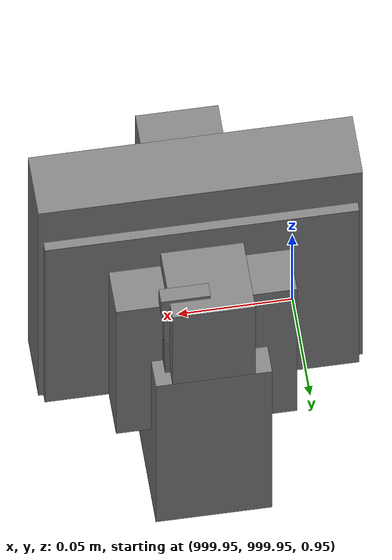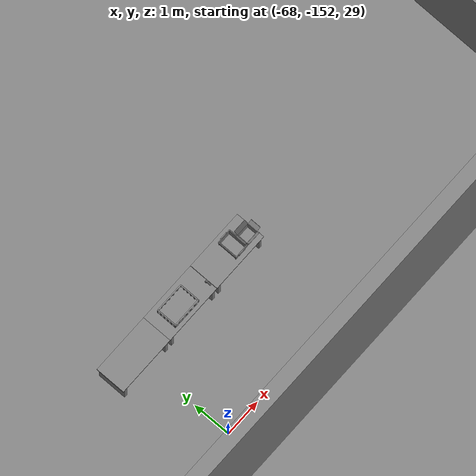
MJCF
<mujoco>
    <option gravity="0.000000000 0.000000000 -9.810000420" timestep="0.0049999999" integrator="implicitfast" density="1.225" viscosity="1.8000001e-05" noslip_iterations="10" iterations="100" sdf_iterations="50">
        <flag multiccd="disable"/>
    </option>
    <size memory="1000M"/>
    <compiler coordinate="local"/>
    <worldbody>
        <light cutoff="30" pos="0 1 1" dir="0 -1 -2"/>
        <light cutoff="30" pos="0 -1 1" dir="0 1 -2"/>
        <body pos="-64.866622925 -149.383972168 30.183746338" euler="89.999984741 89.999946594 0.000000000" name="openloong_gripper_2f85_fix_base_usda_bluebox_01">
            <geom contype="1" conaffinity="1" density="1000" type="box" material="" rgba="0.500000000 0.500000000 0.500000000 1.000000000" solimp="0.899999976 0.949999988 0.001000000" friction="1.000000000 0.005000000 0.000100000" solref="0.020000000 1.000000000" margin="0" condim="3" group="0" pos="0.276580811 0.187225342 0.000068665" quat="0.707106948 0.000077471 0.707106352 0.000077486" size="0.100000001 0.057999998 0.010000000" name="openloong_gripper_2f85_fix_base_usda_geom_B9D87317_204F_49AB_9926_97CABCEF3D30"/>
            <geom contype="1" conaffinity="1" density="1000" type="box" material="" rgba="0.500000000 0.500000000 0.500000000 1.000000000" solimp="0.899999976 0.949999988 0.001000000" friction="1.000000000 0.005000000 0.000100000" solref="0.020000000 1.000000000" margin="0" condim="3" group="0" pos="0.000000000 0.002883911 0.000000000" quat="0.999999881 0.000000000 0.000000000 0.000000000" size="0.254000008 0.003000000 0.172000006" name="openloong_gripper_2f85_fix_base_usda_geom_CA776399_6A63_4070_8F7A_AD5076A0B30C"/>
            <geom contype="1" conaffinity="1" density="1000" type="box" material="" rgba="0.500000000 0.500000000 0.500000000 1.000000000" solimp="0.899999976 0.949999988 0.001000000" friction="1.000000000 0.005000000 0.000100000" solref="0.020000000 1.000000000" margin="0" condim="3" group="0" pos="0.000000000 0.124874115 0.173484802" quat="0.999796331 0.020176515 -0.000000015 0.000000030" size="0.259999990 0.119999997 0.007000000" name="openloong_gripper_2f85_fix_base_usda_geom_453883C3_CBB5_4E6E_A483_9DD740EB5B7F"/>
            <geom contype="1" conaffinity="1" density="1000" type="box" material="" rgba="0.500000000 0.500000000 0.500000000 1.000000000" solimp="0.899999976 0.949999988 0.001000000" friction="1.000000000 0.005000000 0.000100000" solref="0.020000000 1.000000000" margin="0" condim="3" group="0" pos="0.000000000 0.124874115 -0.173469543" quat="0.999796331 -0.020176545 -0.000000015 0.000000000" size="0.259999990 0.119999997 0.007000000" name="openloong_gripper_2f85_fix_base_usda_geom_2AE622A6_73BA_4207_96D3_398585848080"/>
            <geom contype="1" conaffinity="1" density="1000" type="box" material="" rgba="0.500000000 0.500000000 0.500000000 1.000000000" solimp="0.899999976 0.949999988 0.001000000" friction="1.000000000 0.005000000 0.000100000" solref="0.020000000 1.000000000" margin="0" condim="3" group="0" pos="0.000000000 0.214008331 0.188980103" quat="0.999912977 0.013176724 0.000000015 0.000000000" size="0.259999990 0.029999999 0.012500000" name="openloong_gripper_2f85_fix_base_usda_geom_349A2DA0_F9CF_42D4_813D_D2F5BA681678"/>
            <geom contype="1" conaffinity="1" density="1000" type="box" material="" rgba="0.500000000 0.500000000 0.500000000 1.000000000" solimp="0.899999976 0.949999988 0.001000000" friction="1.000000000 0.005000000 0.000100000" solref="0.020000000 1.000000000" margin="0" condim="3" group="0" pos="-0.258361816 0.125289917 0.001876831" quat="0.702796936 -0.020792112 0.710783124 0.020769298" size="0.189999998 0.119999997 0.009000000" name="openloong_gripper_2f85_fix_base_usda_geom_EA373CA9_9424_4430_AC83_F0DC15664CF9"/>
            <geom contype="1" conaffinity="1" density="1000" type="box" material="" rgba="0.500000000 0.500000000 0.500000000 1.000000000" solimp="0.899999976 0.949999988 0.001000000" friction="1.000000000 0.005000000 0.000100000" solref="0.020000000 1.000000000" margin="0" condim="3" group="0" pos="0.000000000 0.214008331 -0.188980103" quat="0.999912977 -0.013176769 0.000000030 0.000000015" size="0.259999990 0.029999999 0.012500000" name="openloong_gripper_2f85_fix_base_usda_geom_BA80EA2B_A722_40DB_ABBB_F1BFC472C528"/>
            <geom contype="1" conaffinity="1" density="1000" type="box" material="" rgba="0.500000000 0.500000000 0.500000000 1.000000000" solimp="0.899999976 0.949999988 0.001000000" friction="1.000000000 0.005000000 0.000100000" solref="0.020000000 1.000000000" margin="0" condim="3" group="0" pos="-0.276611328 0.187225342 0.000068665" quat="0.707106650 0.000077441 0.707106709 0.000077456" size="0.100000001 0.057999998 0.010000000" name="openloong_gripper_2f85_fix_base_usda_geom_E134F8E9_8C96_452E_84F2_60C06BAFA0AC"/>
            <geom contype="1" conaffinity="1" density="1000" type="box" material="" rgba="0.500000000 0.500000000 0.500000000 1.000000000" solimp="0.899999976 0.949999988 0.001000000" friction="1.000000000 0.005000000 0.000100000" solref="0.020000000 1.000000000" margin="0" condim="3" group="0" pos="0.258331299 0.125289917 0.001876831" quat="0.702851415 0.018856421 0.710823774 -0.019329369" size="0.189999998 0.119999997 0.009000000" name="openloong_gripper_2f85_fix_base_usda_geom_BC85607E_461E_4FE6_8999_59734E65D661"/>
            <freejoint name="openloong_gripper_2f85_fix_base_usda_bluebox_01_joint"/>
            <site size="0.005000000 0.005000000 0.005000000" rgba="0.500000000 0.500000000 0.500000000 1.000000000" pos="0.000000000 0.000000000 0.000000000" quat="0.999961913 0.008726534 0.000000000 0.000000000" group="0" type="sphere" name="openloong_gripper_2f85_fix_base_usda_bluebox_01site"/>
        </body>
        <body pos="-64.496299744 -149.491867065 30.235729218" euler="0.000000000 0.000000000 89.999946594" name="openloong_gripper_2f85_fix_base_usda_cardboardbox_01">
            <geom contype="1" conaffinity="1" density="1000" type="box" material="" rgba="0.500000000 0.500000000 0.500000000 1.000000000" solimp="0.899999976 0.949999988 0.001000000" friction="1.000000000 0.005000000 0.000100000" solref="0.020000000 1.000000000" margin="0" condim="3" group="0" pos="-0.003166199 -0.004086494 0.005052090" quat="1.000000000 0.000000000 0.000000000 0.000000000" size="0.142499998 0.177500010 0.005000000" name="openloong_gripper_2f85_fix_base_usda_geom_59518E5A_6C18_495D_908B_FA447712A116"/>
            <geom contype="1" conaffinity="1" density="1000" type="box" material="" rgba="0.500000000 0.500000000 0.500000000 1.000000000" solimp="0.899999976 0.949999988 0.001000000" friction="1.000000000 0.005000000 0.000100000" solref="0.020000000 1.000000000" margin="0" condim="3" group="0" pos="-0.003166199 0.170316696 0.150570869" quat="1.000000000 0.000000000 0.000000000 0.000000000" size="0.142499998 0.005000000 0.149999991" name="openloong_gripper_2f85_fix_base_usda_geom_31D048EC_E676_44A5_AE3A_0F468C8C1155"/>
            <geom contype="1" conaffinity="1" density="1000" type="box" material="" rgba="0.500000000 0.500000000 0.500000000 1.000000000" solimp="0.899999976 0.949999988 0.001000000" friction="1.000000000 0.005000000 0.000100000" solref="0.020000000 1.000000000" margin="0" condim="3" group="0" pos="-0.147399902 -0.005307198 0.150570869" quat="1.000000000 0.000000000 0.000000000 0.000000000" size="0.005000000 0.177500010 0.149999991" name="openloong_gripper_2f85_fix_base_usda_geom_57C61117_C98C_4FC5_A24A_272742B45196"/>
            <geom contype="1" conaffinity="1" density="1000" type="box" material="" rgba="0.500000000 0.500000000 0.500000000 1.000000000" solimp="0.899999976 0.949999988 0.001000000" friction="1.000000000 0.005000000 0.000100000" solref="0.020000000 1.000000000" margin="0" condim="3" group="0" pos="0.140275955 -0.005307198 0.150570869" quat="1.000000000 0.000000000 0.000000000 0.000000000" size="0.005000000 0.177500010 0.149999991" name="openloong_gripper_2f85_fix_base_usda_geom_9E092F36_2FA7_4955_9CDD_41097D94D599"/>
            <geom contype="1" conaffinity="1" density="1000" type="box" material="" rgba="0.500000000 0.500000000 0.500000000 1.000000000" solimp="0.899999976 0.949999988 0.001000000" friction="1.000000000 0.005000000 0.000100000" solref="0.020000000 1.000000000" margin="0" condim="3" group="0" pos="-0.003166199 -0.181550980 0.150570869" quat="1.000000000 0.000000000 0.000000000 0.000000000" size="0.142499998 0.005000000 0.149999991" name="openloong_gripper_2f85_fix_base_usda_geom_90C9DD37_BCBD_4643_BC26_26590DD3CF90"/>
            <freejoint name="openloong_gripper_2f85_fix_base_usda_cardboardbox_01_joint"/>
            <site size="0.005000000 0.005000000 0.005000000" rgba="0.500000000 0.500000000 0.500000000 1.000000000" pos="0.000000000 0.000000000 0.000000000" quat="0.999961913 0.008726535 0.000000000 0.000000000" group="0" type="sphere" name="openloong_gripper_2f85_fix_base_usda_site_493855E4_0C12_458D_86D9_89423E14239A"/>
            <body pos="0.139160156 -0.004048347 0.301930904" euler="-179.999954224 49.383502960 179.999954224" name="openloong_gripper_2f85_fix_base_usda_A1_006">
                <geom contype="1" conaffinity="1" density="1000" type="box" material="" rgba="0.500000000 0.500000000 0.500000000 1.000000000" solimp="0.899999976 0.949999988 0.001000000" friction="1.000000000 0.005000000 0.000100000" solref="0.020000000 1.000000000" margin="0" condim="3" group="0" pos="-0.071587563 0.000009537 0.001745224" quat="0.999999881 0.000000000 0.000000000 0.000000000" size="0.071249999 0.179999992 0.002500000" name="openloong_gripper_2f85_fix_base_usda_geom_4265D579_1999_4224_BAE6_F481C2E244BD"/>
                <joint armature="0" stiffness="0.07" damping="0.0099999998" axis="0.000000 1.000000 0.000000" type="hinge" name="openloong_gripper_2f85_fix_base_usda_A1_006"/>
            </body>
            <body pos="-0.145902634 -0.004086494 0.301938057" euler="-180.000000000 -60.000011444 -180.000000000" name="openloong_gripper_2f85_fix_base_usda_A2_006">
                <geom contype="1" conaffinity="1" density="1000" type="box" material="" rgba="0.500000000 0.500000000 0.500000000 1.000000000" solimp="0.899999976 0.949999988 0.001000000" friction="1.000000000 0.005000000 0.000100000" solref="0.020000000 1.000000000" margin="0" condim="3" group="0" pos="0.071268082 0.000009537 0.002717972" quat="0.000002921 0.000000000 -0.000000030 0.999999881" size="0.071249999 0.179999992 0.002500000" name="openloong_gripper_2f85_fix_base_usda_geom_8B520E48_24AE_48BF_82E7_3DFB640A1694"/>
                <joint armature="0" stiffness="0.07" damping="0.0099999998" axis="0.000000 1.000000 0.000000" type="hinge" name="openloong_gripper_2f85_fix_base_usda_A2_006"/>
            </body>
            <body pos="-0.003385544 0.175991058 0.301930904" euler="-125.858116150 -0.000004561 0.000002331" name="openloong_gripper_2f85_fix_base_usda_B2_006">
                <geom contype="1" conaffinity="1" density="1000" type="box" material="" rgba="0.500000000 0.500000000 0.500000000 1.000000000" solimp="0.899999976 0.949999988 0.001000000" friction="1.000000000 0.005000000 0.000100000" solref="0.020000000 1.000000000" margin="0" condim="3" group="0" pos="0.000009537 -0.070939064 -0.002470016" quat="0.999614120 0.027776197 -0.000000015 0.000000030" size="0.137500003 0.064999998 0.005000000" name="openloong_gripper_2f85_fix_base_usda_geom_428CE8F2_1B40_4721_B50E_F992F21391AA"/>
                <joint armature="0" stiffness="0.07" damping="0.0099999998" axis="1.000000 0.000000 0.000000" type="hinge" name="openloong_gripper_2f85_fix_base_usda_B2_006"/>
            </body>
            <body pos="-0.003385544 -0.184140205 0.301938057" euler="147.805557251 0.000000000 0.000000000" name="openloong_gripper_2f85_fix_base_usda_B1_006">
                <geom contype="1" conaffinity="1" density="1000" type="box" material="" rgba="0.500000000 0.500000000 0.500000000 1.000000000" solimp="0.899999976 0.949999988 0.001000000" friction="1.000000000 0.005000000 0.000100000" solref="0.020000000 1.000000000" margin="0" condim="3" group="0" pos="-0.000028610 0.070202351 -0.002703667" quat="0.999614179 -0.027776167 0.000000000 0.000000000" size="0.137500003 0.064999998 0.005000000" name="openloong_gripper_2f85_fix_base_usda_geom_411C6E44_240F_4B78_B355_711E14BDC481"/>
                <joint armature="0" stiffness="0.07" damping="0.0099999998" axis="1.000000 0.000000 0.000000" type="hinge" name="openloong_gripper_2f85_fix_base_usda_B1_006"/>
            </body>
        </body>
        <body pos="-65.882858276 -149.481979370 30.229999542" euler="-64.487716675 0.000000000 0.000000000" name="openloong_gripper_2f85_fix_base_usda_Barcode">
            <geom contype="1" conaffinity="1" density="1000" type="box" material="" rgba="0.500000000 0.500000000 0.500000000 1.000000000" solimp="0.899999976 0.949999988 0.001000000" friction="1.000000000 0.005000000 0.000100000" solref="0.020000000 1.000000000" margin="0" condim="3" group="0" pos="0.000000000 0.013038635 0.001419067" quat="0.000000000 0.000000000 0.000000000 1.000000119" size="0.034000002 0.010000000 0.017999999" name="openloong_gripper_2f85_fix_base_usda_geom_975610C7_F769_47A4_9009_3C60F0463742"/>
            <geom contype="1" conaffinity="1" density="1000" type="box" material="" rgba="0.500000000 0.500000000 0.500000000 1.000000000" solimp="0.899999976 0.949999988 0.001000000" friction="1.000000000 0.005000000 0.000100000" solref="0.020000000 1.000000000" margin="0" condim="3" group="0" pos="0.000000000 -0.035301208 -0.007095337" quat="0.000000000 0.000000000 -0.043619365 0.999048233" size="0.028999999 0.010000000 0.020000000" name="openloong_gripper_2f85_fix_base_usda_geom_B0912C61_B4D3_4500_A93C_F76D313B54F1"/>
            <geom contype="1" conaffinity="1" density="1000" type="box" material="" rgba="0.500000000 0.500000000 0.500000000 1.000000000" solimp="0.899999976 0.949999988 0.001000000" friction="1.000000000 0.005000000 0.000100000" solref="0.020000000 1.000000000" margin="0" condim="3" group="0" pos="0.000000000 -0.043411255 -0.011749268" quat="0.922262907 0.386563420 0.000000000 0.000000000" size="0.026000001 0.010000000 0.020000000" name="openloong_gripper_2f85_fix_base_usda_geom_109B5CBC_A716_475B_BB26_F5E67C276EBE"/>
            <geom contype="1" conaffinity="1" density="1000" type="box" material="" rgba="0.500000000 0.500000000 0.500000000 1.000000000" solimp="0.899999976 0.949999988 0.001000000" friction="1.000000000 0.005000000 0.000100000" solref="0.020000000 1.000000000" margin="0" condim="3" group="0" pos="0.000000000 -0.016967773 -0.031860352" quat="0.000000000 0.000000000 0.000000000 1.000000119" size="0.008000000 0.010000000 0.013000000" name="openloong_gripper_2f85_fix_base_usda_geom_B0D0DC0E_7A1F_4015_B7A9_212213E5194C"/>
            <geom contype="1" conaffinity="1" density="1000" type="box" material="" rgba="0.500000000 0.500000000 0.500000000 1.000000000" solimp="0.899999976 0.949999988 0.001000000" friction="1.000000000 0.005000000 0.000100000" solref="0.020000000 1.000000000" margin="0" condim="3" group="0" pos="0.000000000 -0.001869202 0.000312805" quat="0.953716993 0.300705761 0.000000000 0.000000000" size="0.032000002 0.010000000 0.018999999" name="openloong_gripper_2f85_fix_base_usda_geom_3269FC70_A0EF_45A4_9C2B_B432E014B044"/>
            <geom contype="1" conaffinity="1" density="1000" type="box" material="" rgba="0.500000000 0.500000000 0.500000000 1.000000000" solimp="0.899999976 0.949999988 0.001000000" friction="1.000000000 0.005000000 0.000100000" solref="0.020000000 1.000000000" margin="0" condim="3" group="0" pos="0.000000000 -0.019531250 -0.003173828" quat="0.953716993 0.300705761 0.000000000 0.000000000" size="0.030999999 0.010000000 0.020000000" name="openloong_gripper_2f85_fix_base_usda_geom_949A8C9A_954A_40C3_8474_F203DFD628AC"/>
            <geom contype="1" conaffinity="1" density="1000" type="box" material="" rgba="0.500000000 0.500000000 0.500000000 1.000000000" solimp="0.899999976 0.949999988 0.001000000" friction="1.000000000 0.005000000 0.000100000" solref="0.020000000 1.000000000" margin="0" condim="3" group="0" pos="0.000000000 -0.035301208 -0.007095337" quat="0.953716993 0.300705761 0.000000000 0.000000000" size="0.028999999 0.010000000 0.020000000" name="openloong_gripper_2f85_fix_base_usda_geom_0E2E16CB_D92C_4760_94BC_A1E6BCC23F70"/>
            <geom contype="1" conaffinity="1" density="1000" type="box" material="" rgba="0.500000000 0.500000000 0.500000000 1.000000000" solimp="0.899999976 0.949999988 0.001000000" friction="1.000000000 0.005000000 0.000100000" solref="0.020000000 1.000000000" margin="0" condim="3" group="0" pos="0.000000000 -0.042617798 -0.071121216" quat="0.000000000 0.000000000 0.000000000 1.000000119" size="0.013000000 0.021000000 0.059999999" name="openloong_gripper_2f85_fix_base_usda_geom_46FBF050_2750_47CF_B29A_BE6DD9405FC2"/>
            <freejoint name="openloong_gripper_2f85_fix_base_usda_Barcode_joint"/>
            <site size="0.005000000 0.005000000 0.005000000" rgba="0.500000000 0.500000000 0.500000000 1.000000000" pos="0.000000000 0.000000000 0.000000000" quat="1.000000000 0.000000000 0.000000000 0.000000000" group="0" type="sphere" name="openloong_gripper_2f85_fix_base_usda_Barcode_site"/>
        </body>
        <body pos="-66.745018005 -149.392349243 30.184000015" euler="0.000000000 0.000000000 89.999946594" name="[22333601420745]_Basket_01">
            <geom contype="1" conaffinity="1" density="1000" type="box" material="" rgba="0.500000000 0.500000000 0.500000000 1.000000000" solimp="0.899999976 0.949999988 0.001000000" friction="1.000000000 0.005000000 0.000100000" solref="0.020000000 1.000000000" margin="0" condim="3" group="0" pos="-0.052425385 0.389207840 0.089787483" quat="0.707107008 0.000000000 0.000000000 0.707106411" size="0.014249999 0.014249999 0.059999999" name="[22333601420745]_geom_62ACEA56_725D_4BAF_84D2_9695CEB59D62"/>
            <geom contype="1" conaffinity="1" density="1000" type="box" material="" rgba="0.500000000 0.500000000 0.500000000 1.000000000" solimp="0.899999976 0.949999988 0.001000000" friction="1.000000000 0.005000000 0.000100000" solref="0.020000000 1.000000000" margin="0" condim="3" group="0" pos="0.264015198 -0.133043289 0.089787483" quat="0.707107008 0.000000000 0.000000000 0.707106411" size="0.014249999 0.014249999 0.059999999" name="[22333601420745]_geom_30BA83F2_2AEF_45BD_99A8_E22D6A4BC1FA"/>
            <geom contype="1" conaffinity="1" density="1000" type="box" material="" rgba="0.500000000 0.500000000 0.500000000 1.000000000" solimp="0.899999976 0.949999988 0.001000000" friction="1.000000000 0.005000000 0.000100000" solref="0.020000000 1.000000000" margin="0" condim="3" group="0" pos="-0.264015198 -0.265548706 0.089793205" quat="0.707107008 0.000000000 0.000000000 0.707106411" size="0.014249999 0.014249999 0.059999999" name="[22333601420745]_geom_CB36ED47_224D_4CEC_865B_0ECEFA48C26F"/>
            <geom contype="1" conaffinity="1" density="1000" type="box" material="" rgba="0.500000000 0.500000000 0.500000000 1.000000000" solimp="0.899999976 0.949999988 0.001000000" friction="1.000000000 0.005000000 0.000100000" solref="0.020000000 1.000000000" margin="0" condim="3" group="0" pos="-0.160263062 -0.389322281 0.089793205" quat="0.707107008 0.000000000 0.000000000 0.707106411" size="0.014249999 0.014249999 0.059999999" name="[22333601420745]_geom_F610AA70_242F_4C65_8DAA_DA3C89E966A0"/>
            <geom contype="1" conaffinity="1" density="1000" type="box" material="" rgba="0.500000000 0.500000000 0.500000000 1.000000000" solimp="0.899999976 0.949999988 0.001000000" friction="1.000000000 0.005000000 0.000100000" solref="0.020000000 1.000000000" margin="0" condim="3" group="0" pos="0.162265778 -0.389322281 0.089787483" quat="0.707107008 0.000000000 0.000000000 0.707106411" size="0.014249999 0.014249999 0.059999999" name="[22333601420745]_geom_EF271CAB_5B73_48D6_908F_2E5ADFD3C127"/>
            <geom contype="1" conaffinity="1" density="1000" type="box" material="" rgba="0.500000000 0.500000000 0.500000000 1.000000000" solimp="0.899999976 0.949999988 0.001000000" friction="1.000000000 0.005000000 0.000100000" solref="0.020000000 1.000000000" margin="0" condim="3" group="0" pos="0.264015198 0.389207840 0.089787483" quat="0.707107008 0.000000000 0.000000000 0.707106411" size="0.014249999 0.014249999 0.059999999" name="[22333601420745]_geom_73CB2243_6B2E_4FFD_87B2_E5C289F3B3FC"/>
            <geom contype="1" conaffinity="1" density="1000" type="box" material="" rgba="0.500000000 0.500000000 0.500000000 1.000000000" solimp="0.899999976 0.949999988 0.001000000" friction="1.000000000 0.005000000 0.000100000" solref="0.020000000 1.000000000" margin="0" condim="3" group="0" pos="-0.264015198 -0.133043289 0.089793205" quat="0.707107008 0.000000000 0.000000000 0.707106411" size="0.014249999 0.014249999 0.059999999" name="[22333601420745]_geom_91F9B9B1_3652_470F_9EBD_B299AF6876A6"/>
            <geom contype="1" conaffinity="1" density="1000" type="box" material="" rgba="0.500000000 0.500000000 0.500000000 1.000000000" solimp="0.899999976 0.949999988 0.001000000" friction="1.000000000 0.005000000 0.000100000" solref="0.020000000 1.000000000" margin="0" condim="3" group="0" pos="-0.264026642 0.269256592 0.089793205" quat="0.707107008 0.000000000 0.000000000 0.707106411" size="0.014249999 0.014249999 0.059999999" name="[22333601420745]_geom_A20D7284_1281_4F8E_92FE_BAF945AAB7C4"/>
            <geom contype="1" conaffinity="1" density="1000" type="box" material="" rgba="0.500000000 0.500000000 0.500000000 1.000000000" solimp="0.899999976 0.949999988 0.001000000" friction="1.000000000 0.005000000 0.000100000" solref="0.020000000 1.000000000" margin="0" condim="3" group="0" pos="0.054462433 0.389207840 0.089787483" quat="0.707107008 0.000000000 0.000000000 0.707106411" size="0.014249999 0.014249999 0.059999999" name="[22333601420745]_geom_249FAFB5_4CEF_4DF9_9066_9D5DC76933F1"/>
            <geom contype="1" conaffinity="1" density="1000" type="box" material="" rgba="0.500000000 0.500000000 0.500000000 1.000000000" solimp="0.899999976 0.949999988 0.001000000" friction="1.000000000 0.005000000 0.000100000" solref="0.020000000 1.000000000" margin="0" condim="3" group="0" pos="0.054462433 -0.389322281 0.089787483" quat="0.707107008 0.000000000 0.000000000 0.707106411" size="0.014249999 0.014249999 0.059999999" name="[22333601420745]_geom_F31384C2_5F74_49D0_88AA_2E6EE1CA6B7C"/>
            <geom contype="1" conaffinity="1" density="1000" type="box" material="" rgba="0.500000000 0.500000000 0.500000000 1.000000000" solimp="0.899999976 0.949999988 0.001000000" friction="1.000000000 0.005000000 0.000100000" solref="0.020000000 1.000000000" margin="0" condim="3" group="0" pos="0.264015198 0.269256592 0.089793205" quat="0.707107008 0.000000000 0.000000000 0.707106411" size="0.014249999 0.014249999 0.059999999" name="[22333601420745]_geom_28BA54B4_650F_4F8C_82FE_7714721B6387"/>
            <geom contype="1" conaffinity="1" density="1000" type="box" material="" rgba="0.500000000 0.500000000 0.500000000 1.000000000" solimp="0.899999976 0.949999988 0.001000000" friction="1.000000000 0.005000000 0.000100000" solref="0.020000000 1.000000000" margin="0" condim="3" group="0" pos="0.264015198 -0.389322281 0.089787483" quat="0.707107008 0.000000000 0.000000000 0.707106411" size="0.014249999 0.014249999 0.059999999" name="[22333601420745]_geom_5264E013_2117_4564_A7EF_8951C2887377"/>
            <geom contype="1" conaffinity="1" density="1000" type="box" material="" rgba="0.500000000 0.500000000 0.500000000 1.000000000" solimp="0.899999976 0.949999988 0.001000000" friction="1.000000000 0.005000000 0.000100000" solref="0.020000000 1.000000000" margin="0" condim="3" group="0" pos="0.000000000 0.000000000 0.015998840" quat="0.707107008 0.000000000 0.000000000 0.707106411" size="0.403499991 0.279000014 0.015750000" name="[22333601420745]_geom_29E194F3_DD1F_4EE9_8798_FE3157746744"/>
            <geom contype="1" conaffinity="1" density="1000" type="box" material="" rgba="0.500000000 0.500000000 0.500000000 1.000000000" solimp="0.899999976 0.949999988 0.001000000" friction="1.000000000 0.005000000 0.000100000" solref="0.020000000 1.000000000" margin="0" condim="3" group="0" pos="0.000000000 -0.389476776 0.163619041" quat="0.707107008 0.000000000 0.000000000 0.707106411" size="0.015000000 0.277500004 0.015750000" name="[22333601420745]_geom_925478CD_CEAC_40E0_9DA1_A4F9D2F6C58E"/>
            <geom contype="1" conaffinity="1" density="1000" type="box" material="" rgba="0.500000000 0.500000000 0.500000000 1.000000000" solimp="0.899999976 0.949999988 0.001000000" friction="1.000000000 0.005000000 0.000100000" solref="0.020000000 1.000000000" margin="0" condim="3" group="0" pos="0.162265778 0.389207840 0.089787483" quat="0.707107008 0.000000000 0.000000000 0.707106411" size="0.014249999 0.014249999 0.059999999" name="[22333601420745]_geom_27168DD4_5E01_47E6_83F6_07DFFEC9B8B0"/>
            <geom contype="1" conaffinity="1" density="1000" type="box" material="" rgba="0.500000000 0.500000000 0.500000000 1.000000000" solimp="0.899999976 0.949999988 0.001000000" friction="1.000000000 0.005000000 0.000100000" solref="0.020000000 1.000000000" margin="0" condim="3" group="0" pos="0.000000000 0.389471054 0.163619041" quat="0.707107008 0.000000000 0.000000000 0.707106411" size="0.015000000 0.277500004 0.015750000" name="[22333601420745]_geom_47A88B3D_FF3A_4F54_B0DD_257BC72BE6B5"/>
            <geom contype="1" conaffinity="1" density="1000" type="box" material="" rgba="0.500000000 0.500000000 0.500000000 1.000000000" solimp="0.899999976 0.949999988 0.001000000" friction="1.000000000 0.005000000 0.000100000" solref="0.020000000 1.000000000" margin="0" condim="3" group="0" pos="-0.263511658 0.000000000 0.163619041" quat="0.707107008 0.000000000 0.000000000 0.707106411" size="0.403499991 0.015000000 0.015750000" name="[22333601420745]_geom_51149055_8117_4D4E_8172_FF2694B6E497"/>
            <geom contype="1" conaffinity="1" density="1000" type="box" material="" rgba="0.500000000 0.500000000 0.500000000 1.000000000" solimp="0.899999976 0.949999988 0.001000000" friction="1.000000000 0.005000000 0.000100000" solref="0.020000000 1.000000000" margin="0" condim="3" group="0" pos="-0.264015198 0.141334534 0.089793205" quat="0.707107008 0.000000000 0.000000000 0.707106411" size="0.014249999 0.014249999 0.059999999" name="[22333601420745]_geom_9CF43B87_4814_4DB8_8A23_1EA4AB16E4A8"/>
            <geom contype="1" conaffinity="1" density="1000" type="box" material="" rgba="0.500000000 0.500000000 0.500000000 1.000000000" solimp="0.899999976 0.949999988 0.001000000" friction="1.000000000 0.005000000 0.000100000" solref="0.020000000 1.000000000" margin="0" condim="3" group="0" pos="0.264015198 -0.265548706 0.089787483" quat="0.707107008 0.000000000 0.000000000 0.707106411" size="0.014249999 0.014249999 0.059999999" name="[22333601420745]_geom_F7C4C82D_0136_4B26_B96B_7DE75A5623B2"/>
            <geom contype="1" conaffinity="1" density="1000" type="box" material="" rgba="0.500000000 0.500000000 0.500000000 1.000000000" solimp="0.899999976 0.949999988 0.001000000" friction="1.000000000 0.005000000 0.000100000" solref="0.020000000 1.000000000" margin="0" condim="3" group="0" pos="-0.160263062 0.389207840 0.089787483" quat="0.707107008 0.000000000 0.000000000 0.707106411" size="0.014249999 0.014249999 0.059999999" name="[22333601420745]_geom_73AF6B8D_DCDB_42B9_B0BF_EC552C88D6BB"/>
            <geom contype="1" conaffinity="1" density="1000" type="box" material="" rgba="0.500000000 0.500000000 0.500000000 1.000000000" solimp="0.899999976 0.949999988 0.001000000" friction="1.000000000 0.005000000 0.000100000" solref="0.020000000 1.000000000" margin="0" condim="3" group="0" pos="-0.052425385 -0.389322281 0.089787483" quat="0.707107008 0.000000000 0.000000000 0.707106411" size="0.014249999 0.014249999 0.059999999" name="[22333601420745]_geom_C423C7A5_83A8_4A3B_A565_62B2180423E9"/>
            <geom contype="1" conaffinity="1" density="1000" type="box" material="" rgba="0.500000000 0.500000000 0.500000000 1.000000000" solimp="0.899999976 0.949999988 0.001000000" friction="1.000000000 0.005000000 0.000100000" solref="0.020000000 1.000000000" margin="0" condim="3" group="0" pos="-0.264026642 -0.389322281 0.089793205" quat="0.707107008 0.000000000 0.000000000 0.707106411" size="0.014249999 0.014249999 0.059999999" name="[22333601420745]_geom_51EE80CB_516A_4FF3_B18D_AE1FD116A2EC"/>
            <geom contype="1" conaffinity="1" density="1000" type="box" material="" rgba="0.500000000 0.500000000 0.500000000 1.000000000" solimp="0.899999976 0.949999988 0.001000000" friction="1.000000000 0.005000000 0.000100000" solref="0.020000000 1.000000000" margin="0" condim="3" group="0" pos="0.264015198 0.141334534 0.089787483" quat="0.707107008 0.000000000 0.000000000 0.707106411" size="0.014249999 0.014249999 0.059999999" name="[22333601420745]_geom_0D5C1A60_6C65_4B3E_8C93_4F49EAF1E811"/>
            <geom contype="1" conaffinity="1" density="1000" type="box" material="" rgba="0.500000000 0.500000000 0.500000000 1.000000000" solimp="0.899999976 0.949999988 0.001000000" friction="1.000000000 0.005000000 0.000100000" solref="0.020000000 1.000000000" margin="0" condim="3" group="0" pos="-0.264015198 0.389207840 0.089793205" quat="0.707107008 0.000000000 0.000000000 0.707106411" size="0.014249999 0.014249999 0.059999999" name="[22333601420745]_geom_955BBC77_C010_4228_8AEB_EE287715701A"/>
            <geom contype="1" conaffinity="1" density="1000" type="box" material="" rgba="0.500000000 0.500000000 0.500000000 1.000000000" solimp="0.899999976 0.949999988 0.001000000" friction="1.000000000 0.005000000 0.000100000" solref="0.020000000 1.000000000" margin="0" condim="3" group="0" pos="0.264015198 0.004480362 0.089787483" quat="0.707107008 0.000000000 0.000000000 0.707106411" size="0.014249999 0.014249999 0.059999999" name="[22333601420745]_geom_C0498C77_8C51_4C4D_BDE1_77019B7FDF55"/>
            <geom contype="1" conaffinity="1" density="1000" type="box" material="" rgba="0.500000000 0.500000000 0.500000000 1.000000000" solimp="0.899999976 0.949999988 0.001000000" friction="1.000000000 0.005000000 0.000100000" solref="0.020000000 1.000000000" margin="0" condim="3" group="0" pos="0.263694763 -0.000011444 0.163619041" quat="0.707107008 0.000000000 0.000000000 0.707106411" size="0.403499991 0.015000000 0.015750000" name="[22333601420745]_geom_978B1F35_9795_4F26_AB1B_52177E56778C"/>
            <geom contype="1" conaffinity="1" density="1000" type="box" material="" rgba="0.500000000 0.500000000 0.500000000 1.000000000" solimp="0.899999976 0.949999988 0.001000000" friction="1.000000000 0.005000000 0.000100000" solref="0.020000000 1.000000000" margin="0" condim="3" group="0" pos="-0.264015198 0.004480362 0.089793205" quat="0.707107008 0.000000000 0.000000000 0.707106411" size="0.014249999 0.014249999 0.059999999" name="[22333601420745]_geom_3DB38824_D08F_42B6_B6CD_85A9185F9725"/>
            <freejoint name="[22333601420745]_joint_A58FC7F8_D789_4197_99D1_D6B84FECE40F"/>
        </body>
        <body pos="0.000000000 0.000000000 0.000000000" euler="0.000000000 0.000000000 0.000000000" name="Static Objects_Static Objects">
            <geom contype="1" conaffinity="1" density="1000" type="box" material="" rgba="0.500000000 0.500000000 0.500000000 1.000000000" solimp="0.899999976 0.949999988 0.001000000" friction="1.000000000 0.005000000 0.000100000" solref="0.020000000 1.000000000" margin="0" condim="3" group="0" pos="-67.544113159 -149.365814209 29.727830887" quat="0.500000417 0.499999970 0.499999553 0.499999970" size="0.381000012 0.319999993 0.041000001" name="Static Objects_geom_F0CB5C8F_8936_4C33_ABD8_41E3035C68A1"/>
            <geom contype="1" conaffinity="1" density="1000" type="box" material="" rgba="0.500000000 0.500000000 0.500000000 1.000000000" solimp="0.899999976 0.949999988 0.001000000" friction="1.000000000 0.005000000 0.000100000" solref="0.020000000 1.000000000" margin="0" condim="3" group="0" pos="-68.239501953 -149.365814209 30.086868286" quat="0.500000417 0.499999970 0.499999553 0.499999970" size="0.370999992 0.039500002 0.745000005" name="Static Objects_geom_FC1ED67D_153F_47E9_8534_E81E6B16AD27"/>
            <geom contype="1" conaffinity="1" density="1000" type="box" material="" rgba="0.500000000 0.500000000 0.500000000 1.000000000" solimp="0.899999976 0.949999988 0.001000000" friction="1.000000000 0.005000000 0.000100000" solref="0.020000000 1.000000000" margin="0" condim="3" group="0" pos="-68.239501953 -149.365814209 30.147235870" quat="0.500000417 0.499999970 0.499999553 0.499999970" size="0.400000006 0.022000000 0.800000012" name="Static Objects_geom_75DB5698_2D7F_48B2_893A_79C992D5864D"/>
            <geom contype="1" conaffinity="1" density="1000" type="box" material="" rgba="0.500000000 0.500000000 0.500000000 1.000000000" solimp="0.899999976 0.949999988 0.001000000" friction="1.000000000 0.005000000 0.000100000" solref="0.020000000 1.000000000" margin="0" condim="3" group="0" pos="-68.934890747 -149.365814209 29.727830887" quat="0.500000417 0.499999970 0.499999553 0.499999970" size="0.381000012 0.319999993 0.041000001" name="Static Objects_geom_0FE06F77_73D5_4D16_86C8_4B35998CBEDC"/>
            <geom contype="1" conaffinity="1" density="1000" type="box" material="" rgba="0.500000000 0.500000000 0.500000000 1.000000000" solimp="0.899999976 0.949999988 0.001000000" friction="1.000000000 0.005000000 0.000100000" solref="0.020000000 1.000000000" margin="0" condim="3" group="0" pos="-68.239501953 -149.365814209 29.561563492" quat="0.500000417 0.499999970 0.499999553 0.499999970" size="0.020000000 0.022000000 0.660000026" name="Static Objects_geom_63961731_3ECB_46D9_ACFA_C33A85FBEFA3"/>
            <geom contype="1" conaffinity="1" density="1000" type="box" material="" rgba="0.500000000 0.500000000 0.500000000 1.000000000" solimp="0.899999976 0.949999988 0.001000000" friction="1.000000000 0.005000000 0.000100000" solref="0.020000000 1.000000000" margin="0" condim="3" group="0" pos="-65.945671082 -149.365814209 29.727830887" quat="0.500000417 0.499999970 0.499999553 0.499999970" size="0.381000012 0.319999993 0.041000001" name="Static Objects_geom_830D1721_1B94_4FEA_9631_7D552B09831B"/>
            <geom contype="1" conaffinity="1" density="1000" type="box" material="" rgba="0.500000000 0.500000000 0.500000000 1.000000000" solimp="0.899999976 0.949999988 0.001000000" friction="1.000000000 0.005000000 0.000100000" solref="0.020000000 1.000000000" margin="0" condim="3" group="0" pos="-66.641059875 -149.365814209 30.086868286" quat="0.500000417 0.499999970 0.499999553 0.499999970" size="0.370999992 0.039500002 0.745000005" name="Static Objects_geom_4CE70D5E_C620_455B_B6D1_0119C109147C"/>
            <geom contype="1" conaffinity="1" density="1000" type="box" material="" rgba="0.500000000 0.500000000 0.500000000 1.000000000" solimp="0.899999976 0.949999988 0.001000000" friction="1.000000000 0.005000000 0.000100000" solref="0.020000000 1.000000000" margin="0" condim="3" group="0" pos="-66.641059875 -149.365814209 30.147235870" quat="0.500000417 0.499999970 0.499999553 0.499999970" size="0.400000006 0.022000000 0.800000012" name="Static Objects_geom_11238804_52DC_4928_8AF1_E7564A7C0C9C"/>
            <geom contype="1" conaffinity="1" density="1000" type="box" material="" rgba="0.500000000 0.500000000 0.500000000 1.000000000" solimp="0.899999976 0.949999988 0.001000000" friction="1.000000000 0.005000000 0.000100000" solref="0.020000000 1.000000000" margin="0" condim="3" group="0" pos="-67.336448669 -149.365814209 29.727830887" quat="0.500000417 0.499999970 0.499999553 0.499999970" size="0.381000012 0.319999993 0.041000001" name="Static Objects_geom_702AB2B1_6F70_43A7_8B6E_D4204A6A14DA"/>
            <geom contype="1" conaffinity="1" density="1000" type="box" material="" rgba="0.500000000 0.500000000 0.500000000 1.000000000" solimp="0.899999976 0.949999988 0.001000000" friction="1.000000000 0.005000000 0.000100000" solref="0.020000000 1.000000000" margin="0" condim="3" group="0" pos="-66.641059875 -149.365814209 29.561563492" quat="0.500000417 0.499999970 0.499999553 0.499999970" size="0.020000000 0.022000000 0.660000026" name="Static Objects_geom_890477FF_5899_4E5E_9C74_74D67A328942"/>
            <geom contype="1" conaffinity="1" density="1000" type="box" material="" rgba="0.500000000 0.500000000 0.500000000 1.000000000" solimp="0.899999976 0.949999988 0.001000000" friction="1.000000000 0.005000000 0.000100000" solref="0.020000000 1.000000000" margin="0" condim="3" group="0" pos="-64.338577271 -149.365814209 29.727830887" quat="0.500000417 0.499999970 0.499999553 0.499999970" size="0.381000012 0.319999993 0.041000001" name="Static Objects_geom_84BDCF9F_15CA_47EC_AC74_AEB6368A8DDE"/>
            <geom contype="1" conaffinity="1" density="1000" type="box" material="" rgba="0.500000000 0.500000000 0.500000000 1.000000000" solimp="0.899999976 0.949999988 0.001000000" friction="1.000000000 0.005000000 0.000100000" solref="0.020000000 1.000000000" margin="0" condim="3" group="0" pos="-65.033966064 -149.365814209 30.086868286" quat="0.500000417 0.499999970 0.499999553 0.499999970" size="0.370999992 0.039500002 0.745000005" name="Static Objects_geom_B919E4D9_4377_490F_B589_CF7F1F5BE10D"/>
            <geom contype="1" conaffinity="1" density="1000" type="box" material="" rgba="0.500000000 0.500000000 0.500000000 1.000000000" solimp="0.899999976 0.949999988 0.001000000" friction="1.000000000 0.005000000 0.000100000" solref="0.020000000 1.000000000" margin="0" condim="3" group="0" pos="-65.033966064 -149.365814209 30.147235870" quat="0.500000417 0.499999970 0.499999553 0.499999970" size="0.400000006 0.022000000 0.800000012" name="Static Objects_geom_5E1987E4_9AD1_4DD8_A407_78B1EBDC0CF0"/>
            <geom contype="1" conaffinity="1" density="1000" type="box" material="" rgba="0.500000000 0.500000000 0.500000000 1.000000000" solimp="0.899999976 0.949999988 0.001000000" friction="1.000000000 0.005000000 0.000100000" solref="0.020000000 1.000000000" margin="0" condim="3" group="0" pos="-65.729354858 -149.365814209 29.727830887" quat="0.500000417 0.499999970 0.499999553 0.499999970" size="0.381000012 0.319999993 0.041000001" name="Static Objects_geom_D30D4BEB_268D_4CA3_B415_D176B20D0FEA"/>
            <geom contype="1" conaffinity="1" density="1000" type="box" material="" rgba="0.500000000 0.500000000 0.500000000 1.000000000" solimp="0.899999976 0.949999988 0.001000000" friction="1.000000000 0.005000000 0.000100000" solref="0.020000000 1.000000000" margin="0" condim="3" group="0" pos="-65.033966064 -149.365814209 29.561563492" quat="0.500000417 0.499999970 0.499999553 0.499999970" size="0.020000000 0.022000000 0.660000026" name="Static Objects_geom_A3CEAB26_8BCF_4D7A_8F9F_3C7E20F9DDFF"/>
            <geom contype="1" conaffinity="1" density="1000" type="box" material="" rgba="0.500000000 0.500000000 0.500000000 1.000000000" solimp="0.899999976 0.949999988 0.001000000" friction="1.000000000 0.005000000 0.000100000" solref="0.020000000 1.000000000" margin="0" condim="3" group="0" pos="-61.754566193 -137.853729248 33.906845093" quat="0.707107067 0.000000000 0.000000000 0.707106471" size="0.759999990 0.759999990 4.500000000" name="Static Objects_geom_5DFAAA7C_3723_4D60_982C_3E85DCD3735A"/>
            <geom contype="1" conaffinity="1" density="1000" type="box" material="" rgba="0.500000000 0.500000000 0.500000000 1.000000000" solimp="0.899999976 0.949999988 0.001000000" friction="1.000000000 0.005000000 0.000100000" solref="0.020000000 1.000000000" margin="0" condim="3" group="0" pos="-57.511135101 -144.927108765 31.707921982" quat="1.000000000 0.000000000 0.000000000 0.000000000" size="0.200000003 8.000000000 2.299999952" name="Static Objects_geom_233F2174_2AAD_4D9A_BFB0_7494A0C01838"/>
            <geom contype="1" conaffinity="1" density="1000" type="box" material="" rgba="0.500000000 0.500000000 0.500000000 1.000000000" solimp="0.899999976 0.949999988 0.001000000" friction="1.000000000 0.005000000 0.000100000" solref="0.020000000 1.000000000" margin="0" condim="3" group="0" pos="-80.517646790 -157.574050903 31.688196182" quat="0.707107067 0.000000000 0.000000000 0.707106471" size="0.600000024 0.600000024 2.299999952" name="Static Objects_geom_A5FC2C96_A185_49A2_98D9_2815F8F494F0"/>
            <geom contype="1" conaffinity="1" density="1000" type="box" material="" rgba="0.500000000 0.500000000 0.500000000 1.000000000" solimp="0.899999976 0.949999988 0.001000000" friction="1.000000000 0.005000000 0.000100000" solref="0.020000000 1.000000000" margin="0" condim="3" group="0" pos="-80.711044312 -147.414932251 31.666158676" quat="1.000000000 0.000000000 0.000000000 0.000000000" size="0.200000003 10.000000000 2.299999952" name="Static Objects_geom_9C916CE3_424B_4290_A3C7_7F5FA518559B"/>
            <geom contype="1" conaffinity="1" density="1000" type="box" material="" rgba="0.500000000 0.500000000 0.500000000 1.000000000" solimp="0.899999976 0.949999988 0.001000000" friction="1.000000000 0.005000000 0.000100000" solref="0.020000000 1.000000000" margin="0" condim="3" group="0" pos="-57.687217712 -137.434692383 31.688196182" quat="0.707107067 0.000000000 0.000000000 0.707106471" size="0.600000024 0.600000024 2.299999952" name="Static Objects_geom_249123AC_6AFA_4567_BFCB_728F0317E822"/>
            <geom contype="1" conaffinity="1" density="1000" type="box" material="" rgba="0.500000000 0.500000000 0.500000000 1.000000000" solimp="0.899999976 0.949999988 0.001000000" friction="1.000000000 0.005000000 0.000100000" solref="0.020000000 1.000000000" margin="0" condim="3" group="0" pos="-69.537033081 -140.263229370 31.714921951" quat="0.707107067 0.000000000 0.000000000 0.707106471" size="0.759999990 4.500000000 2.299999952" name="Static Objects_geom_9091CAA9_D1D9_4F6E_B636_DB80F55F344D"/>
            <geom contype="1" conaffinity="1" density="1000" type="box" material="" rgba="0.500000000 0.500000000 0.500000000 1.000000000" solimp="0.899999976 0.949999988 0.001000000" friction="1.000000000 0.005000000 0.000100000" solref="0.020000000 1.000000000" margin="0" condim="3" group="0" pos="-80.073638916 -137.853713989 33.906845093" quat="0.707107067 0.000000000 0.000000000 0.707106471" size="0.759999990 0.759999990 4.500000000" name="Static Objects_geom_58EBD20A_8332_4FB5_80C9_B9C404C5F3B1"/>
            <geom contype="1" conaffinity="1" density="1000" type="box" material="" rgba="0.500000000 0.500000000 0.500000000 1.000000000" solimp="0.899999976 0.949999988 0.001000000" friction="1.000000000 0.005000000 0.000100000" solref="0.020000000 1.000000000" margin="0" condim="3" group="0" pos="-73.406707764 -155.734664917 31.707921982" quat="1.000000000 0.000000000 0.000000000 0.000000000" size="0.200000003 3.000000000 2.299999952" name="Static Objects_geom_03F48A2B_BD9A_4B01_82F1_D6AAEABD642D"/>
            <geom contype="1" conaffinity="1" density="1000" type="box" material="" rgba="0.500000000 0.500000000 0.500000000 1.000000000" solimp="0.899999976 0.949999988 0.001000000" friction="1.000000000 0.005000000 0.000100000" solref="0.020000000 1.000000000" margin="0" condim="3" group="0" pos="-68.497543335 -137.448257446 31.707921982" quat="0.707107067 0.000000000 0.000000000 0.707106471" size="0.200000003 14.000000000 2.299999952" name="Static Objects_geom_9AD04B0F_4520_4E86_A43A_6331EEA13265"/>
            <geom contype="1" conaffinity="1" density="1000" type="cylinder" material="" rgba="0.500000000 0.500000000 0.500000000 1.000000000" solimp="0.899999976 0.949999988 0.001000000" friction="1.000000000 0.005000000 0.000100000" solref="0.020000000 1.000000000" margin="0" condim="3" group="0" pos="-68.868522644 -142.134506226 31.711090088" quat="0.707107067 0.000000000 0.000000000 0.707106471" size="0.509999990 2.299999952 1.000000000" name="Static Objects_geom_1A536FE8_92B9_4BC8_AC6C_36EF051DA671"/>
            <geom contype="1" conaffinity="1" density="1000" type="plane" material="" rgba="0.500000000 0.500000000 0.500000000 1.000000000" solimp="0.899999976 0.949999988 0.001000000" friction="1.000000000 0.005000000 0.000100000" solref="0.020000000 1.000000000" margin="0" condim="3" group="0" pos="-72.873703003 -147.131927490 29.409669876" quat="1.000000000 0.000000000 0.000000000 0.000000000" size="18.000000000 14.000000000 1.000000000" name="Static Objects_geom_651F8F24_AEB5_4EEE_9DE7_95772403F2B6"/>
            <geom contype="1" conaffinity="1" density="1000" type="box" material="" rgba="0.500000000 0.500000000 0.500000000 1.000000000" solimp="0.899999976 0.949999988 0.001000000" friction="1.000000000 0.005000000 0.000100000" solref="0.020000000 1.000000000" margin="0" condim="3" group="0" pos="-79.943580627 -157.782272339 31.707921982" quat="0.707107067 0.000000000 0.000000000 0.707106471" size="0.200000003 7.000000000 2.299999952" name="Static Objects_geom_76C62F8A_BB84_4FA7_9B28_999D1042EE8E"/>
            <geom contype="1" conaffinity="1" density="1000" type="box" material="" rgba="0.500000000 0.500000000 0.500000000 1.000000000" solimp="0.899999976 0.949999988 0.001000000" friction="1.000000000 0.005000000 0.000100000" solref="0.020000000 1.000000000" margin="0" condim="3" group="0" pos="-65.421028137 -152.903442383 31.707921982" quat="0.707107067 0.000000000 0.000000000 0.707106471" size="0.200000003 7.800000191 2.299999952" name="Static Objects_geom_8D968184_7FAD_48BF_B46E_B82C5B1468CC"/>
            <geom contype="1" conaffinity="1" density="1000" type="box" material="" rgba="0.500000000 0.500000000 0.500000000 1.000000000" solimp="0.899999976 0.949999988 0.001000000" friction="1.000000000 0.005000000 0.000100000" solref="0.020000000 1.000000000" margin="0" condim="3" group="0" pos="-74.776908875 -149.964416504 31.688196182" quat="1.000000000 0.000000000 0.000000000 0.000000000" size="0.600000024 0.409999996 2.299999952" name="Static Objects_geom_8A65AA47_2A28_48D0_A525_AADEF196148C"/>
            <geom contype="1" conaffinity="1" density="1000" type="cylinder" material="" rgba="0.500000000 0.500000000 0.500000000 1.000000000" solimp="0.899999976 0.949999988 0.001000000" friction="1.000000000 0.005000000 0.000100000" solref="0.020000000 1.000000000" margin="0" condim="3" group="0" pos="-60.161884308 -142.134506226 31.711090088" quat="0.707107067 0.000000000 0.000000000 0.707106471" size="0.509999990 2.299999952 1.000000000" name="Static Objects_geom_6436D4DA_ABAD_4A5E_9709_E4313AD0F270"/>
            <geom contype="1" conaffinity="1" density="1000" type="cylinder" material="" rgba="0.500000000 0.500000000 0.500000000 1.000000000" solimp="0.899999976 0.949999988 0.001000000" friction="1.000000000 0.005000000 0.000100000" solref="0.020000000 1.000000000" margin="0" condim="3" group="0" pos="-75.382453918 -149.963455200 31.711090088" quat="0.707107067 0.000000000 0.000000000 0.707106471" size="0.409999996 2.299999952 1.000000000" name="Static Objects_geom_1E7EB023_B037_446F_9BA7_5F74B557CEAD"/>
            <geom contype="1" conaffinity="1" density="1000" type="cylinder" material="" rgba="0.500000000 0.500000000 0.500000000 1.000000000" solimp="0.899999976 0.949999988 0.001000000" friction="1.000000000 0.005000000 0.000100000" solref="0.020000000 1.000000000" margin="0" condim="3" group="0" pos="-74.154960632 -149.963455200 31.711090088" quat="0.707107067 0.000000000 0.000000000 0.707106471" size="0.409999996 2.299999952 1.000000000" name="Static Objects_geom_D3087D2F_EBA3_4C70_89CD_801FAA78A7EA"/>
            <geom contype="1" conaffinity="1" density="1000" type="cylinder" material="" rgba="0.500000000 0.500000000 0.500000000 1.000000000" solimp="0.899999976 0.949999988 0.001000000" friction="1.000000000 0.005000000 0.000100000" solref="0.020000000 1.000000000" margin="0" condim="3" group="0" pos="-77.566612244 -142.134506226 31.711090088" quat="0.707107067 0.000000000 0.000000000 0.707106471" size="0.509999990 2.299999952 1.000000000" name="Static Objects_geom_2EAC99EB_F730_45F0_8997_1C87CE8F9324"/>
        </body>
        <body pos="-66.288162231 -149.062377930 31.167663574" euler="84.678771973 71.488342285 114.049125671" mocap="true" name="spotlight6_SpotLight"/>
        <body pos="1000.000000000 1000.000000000 1.000000000" euler="0.000011953 0.000005123 -179.999984741" name="openloong_gripper_2f85_fix_base_usda_intel_box">
            <geom contype="1" conaffinity="1" density="1000" type="box" material="" rgba="0.500000000 0.500000000 0.500000000 1.000000000" solimp="0.899999976 0.949999988 0.001000000" friction="1.000000000 0.005000000 0.000100000" solref="0.020000000 1.000000000" margin="0" condim="3" group="0" pos="0.000000000 -0.000067139 0.000082284" quat="0.707106709 0.000000225 0.000000253 0.707106650" size="0.052800003 0.025300000 0.052800003" name="openloong_gripper_2f85_fix_base_usda_geom_4D7CBA16_3583_4238_BF8A_5F570506A14E"/>
            <freejoint name="openloong_gripper_2f85_fix_base_usda_intel_box_joint"/>
            <site size="0.005000000 0.005000000 0.005000000" rgba="0.500000000 0.500000000 0.500000000 1.000000000" pos="0.000000000 0.000000000 0.000000000" quat="0.999961913 0.008726500 0.000000000 0.000000000" group="0" type="sphere" name="openloong_gripper_2f85_fix_base_usda_intel_boxsite"/>
        </body>
        <body pos="1000.000000000 1000.000000000 1.000000000" euler="0.000000000 0.000000000 180.000000000" name="openloong_gripper_2f85_fix_base_usda_wifi_box">
            <geom contype="1" conaffinity="1" density="1000" type="box" material="" rgba="0.500000000 0.500000000 0.500000000 1.000000000" solimp="0.899999976 0.949999988 0.001000000" friction="1.000000000 0.005000000 0.000100000" solref="0.020000000 1.000000000" margin="0" condim="3" group="0" pos="0.000000000 0.000000000 0.058978677" quat="0.000000000 0.000000047 0.000000000 1.000000000" size="0.068499997 0.018999999 0.059000000" name="openloong_gripper_2f85_fix_base_usda_geom_999147FA_A4E4_4BCA_88C6_53468A208B90"/>
            <freejoint name="openloong_gripper_2f85_fix_base_usda_wifi_box_joint"/>
            <site size="0.005000000 0.005000000 0.005000000" rgba="0.500000000 0.500000000 0.500000000 1.000000000" pos="0.000000000 0.000000000 0.000000000" quat="0.999961913 0.008726500 0.000000000 0.000000000" group="0" type="sphere" name="openloong_gripper_2f85_fix_base_usda_wifi_boxsite"/>
        </body>
        <body pos="1000.000000000 999.999938965 1.000000000" euler="0.000000000 0.000000000 180.000000000" name="openloong_gripper_2f85_fix_base_usda_intelcore_i5">
            <geom contype="1" conaffinity="1" density="1000" type="box" material="" rgba="0.500000000 0.500000000 0.500000000 1.000000000" solimp="0.899999976 0.949999988 0.001000000" friction="1.000000000 0.005000000 0.000100000" solref="0.020000000 1.000000000" margin="0" condim="3" group="0" pos="0.000000000 0.000000000 0.051722717" quat="0.707106709 0.000000000 0.000000000 -0.707106769" size="0.052800000 0.018080002 0.052800000" name="openloong_gripper_2f85_fix_base_usda_geom_7E90C70A_4EB2_46D9_83BA_6791283CCCE7"/>
            <freejoint name="openloong_gripper_2f85_fix_base_usda_intelcore_i5_joint"/>
            <site size="0.005000000 0.005000000 0.005000000" rgba="0.500000000 0.500000000 0.500000000 1.000000000" pos="0.000000000 0.000000000 0.000000000" quat="0.999961913 0.008726534 0.000000000 0.000000000" group="0" type="sphere" name="openloong_gripper_2f85_fix_base_usda_intelcore_i5site"/>
        </body>
        <body pos="-66.267417908 -149.079711914 31.168392181" euler="176.593109131 21.894971848 -47.088031769" mocap="true" name="spotlight1_SpotLight"/>
        <body pos="1000.000000000 1000.000000000 1.000000000" euler="0.000000000 0.000000000 180.000000000" name="openloong_gripper_2f85_fix_base_usda_cpu_fan">
            <geom contype="1" conaffinity="1" density="1000" type="box" material="" rgba="0.500000000 0.500000000 0.500000000 1.000000000" solimp="0.899999976 0.949999988 0.001000000" friction="1.000000000 0.005000000 0.000100000" solref="0.020000000 1.000000000" margin="0" condim="3" group="0" pos="0.000000000 0.000000000 0.070034981" quat="0.000000000 0.000000000 0.000000000 1.000000000" size="0.070700005 0.014699999 0.070700005" name="openloong_gripper_2f85_fix_base_usda_geom_155C88A2_52F4_4A58_8FA4_F36570496C5A"/>
            <freejoint name="openloong_gripper_2f85_fix_base_usda_cpu_fan_joint"/>
            <site size="0.005000000 0.005000000 0.005000000" rgba="0.500000000 0.500000000 0.500000000 1.000000000" pos="0.000000000 0.000000000 0.000000000" quat="0.999961913 0.008726535 0.000000000 0.000000000" group="0" type="sphere" name="openloong_gripper_2f85_fix_base_usda_cpu_fancsite"/>
        </body>
        <body pos="1000.000000000 1000.000000000 1.000000000" euler="0.000000000 0.000000000 180.000000000" name="openloong_gripper_2f85_fix_base_usda_battery_01">
            <geom contype="1" conaffinity="1" density="1000" type="box" material="" rgba="0.500000000 0.500000000 0.500000000 1.000000000" solimp="0.899999976 0.949999988 0.001000000" friction="1.000000000 0.005000000 0.000100000" solref="0.020000000 1.000000000" margin="0" condim="3" group="0" pos="-0.011123657 -0.041940309 0.101691343" quat="1.000000000 0.000000000 0.000000000 0.000000000" size="0.010800000 0.003375000 0.004725000" name="openloong_gripper_2f85_fix_base_usda_geom_73AA1287_5B21_43C0_A1CD_E2AC70978811"/>
            <geom contype="1" conaffinity="1" density="1000" type="box" material="" rgba="0.500000000 0.500000000 0.500000000 1.000000000" solimp="0.899999976 0.949999988 0.001000000" friction="1.000000000 0.005000000 0.000100000" solref="0.020000000 1.000000000" margin="0" condim="3" group="0" pos="-0.010876465 -0.044247437 0.047066893" quat="0.998702705 -0.050920475 0.000000000 0.000000000" size="0.009450001 0.002700000 0.024975000" name="openloong_gripper_2f85_fix_base_usda_geom_D4F6F3A5_D37E_4BB9_B7D3_A800B5375BFE"/>
            <geom contype="1" conaffinity="1" density="1000" type="box" material="" rgba="0.500000000 0.500000000 0.500000000 1.000000000" solimp="0.899999976 0.949999988 0.001000000" friction="1.000000000 0.005000000 0.000100000" solref="0.020000000 1.000000000" margin="0" condim="3" group="0" pos="-0.001235962 -0.000659180 0.047381196" quat="1.000000000 0.000000000 0.000000000 0.000000000" size="0.039420001 0.039150000 0.047250003" name="openloong_gripper_2f85_fix_base_usda_geom_F5AE4048_E4C3_400C_ADBB_11EBA7CA4B1D"/>
            <geom contype="1" conaffinity="1" density="1000" type="box" material="" rgba="0.500000000 0.500000000 0.500000000 1.000000000" solimp="0.899999976 0.949999988 0.001000000" friction="1.000000000 0.005000000 0.000100000" solref="0.020000000 1.000000000" margin="0" condim="3" group="0" pos="-0.010876465 -0.039138794 0.009851727" quat="1.000000000 0.000000000 0.000000000 0.000000000" size="0.009450001 0.010800000 0.013500000" name="openloong_gripper_2f85_fix_base_usda_geom_93BB0925_8C05_477A_A884_85EFA97FAEDA"/>
            <geom contype="1" conaffinity="1" density="1000" type="box" material="" rgba="0.500000000 0.500000000 0.500000000 1.000000000" solimp="0.899999976 0.949999988 0.001000000" friction="1.000000000 0.005000000 0.000100000" solref="0.020000000 1.000000000" margin="0" condim="3" group="0" pos="-0.010876465 -0.041528322 0.071508206" quat="1.000000000 0.000000000 0.000000000 0.000000000" size="0.009450001 0.002700000 0.027000001" name="openloong_gripper_2f85_fix_base_usda_geom_337BCC31_C280_4CA3_B651_C0F3ACA657E0"/>
            <freejoint name="openloong_gripper_2f85_fix_base_usda_battery_01_joint"/>
            <site size="0.005000000 0.005000000 0.005000000" rgba="0.500000000 0.500000000 0.500000000 1.000000000" pos="0.000000000 0.000000000 0.000000000" quat="0.999961913 0.008726500 0.000000000 0.000000000" group="0" type="sphere" name="openloong_gripper_2f85_fix_base_usda_battery_01site"/>
        </body>
        <body pos="-65.933486938 -149.484252930 31.164838791" euler="82.902923584 22.085685730 136.443542480" mocap="true" name="spotlight4_SpotLight"/>
        <body pos="-66.291030884 -149.869689941 29.018842697" euler="0.000000000 0.000000000 89.999946594" mocap="true" name="openloong_gripper_2f85_fix_base_usda_leftHandMocap"/>
        <body pos="-66.291030884 -149.869689941 29.018842697" euler="0.000000000 0.000000000 89.999946594" mocap="true" name="openloong_gripper_2f85_fix_base_usda_rightHandMocap"/>
        <body pos="-66.291030884 -149.869689941 30.218843460" euler="0.000000000 0.000000000 89.999946594" name="openloong_gripper_2f85_fix_base_usda_base_link">
            <geom contype="1" conaffinity="1" density="1000" type="mesh" material="" rgba="0.783999979 0.783999979 0.783999979 1.000000000" solimp="0.899999976 0.949999988 0.001000000" friction="1.000000000 0.005000000 0.000100000" solref="0.020000000 1.000000000" margin="0" condim="3" group="3" mesh="base_link" pos="0.000000000 0.000000000 0.000000000" quat="1.000000000 0.000000000 0.000000000 0.000000000" size="1.000000000 1.000000000 1.000000000" name="openloong_gripper_2f85_fix_base_usda__geom_7_9F5BABA7_5F65_4204_AC1E_791B59637E89"/>
            <site size="0.005000000 0.005000000 0.005000000" rgba="0.500000000 0.500000000 0.500000000 1.000000000" pos="0.000000000 0.000000000 0.000000000" quat="1.000000000 0.000000000 0.000000000 0.000000000" group="0" type="sphere" name="openloong_gripper_2f85_fix_base_usda_imu"/>
            <inertial mass="22.447001" pos="-0.005664100 -0.001336700 0.238289997" diaginertia="0.374352545 0.277180195 0.220617250" quat="0.999247074 0.035235517 -0.015086859 0.006023135"/>
            <body pos="0.000000000 0.000000000 0.299997330" euler="0.000000000 0.000000000 0.000000000" name="openloong_gripper_2f85_fix_base_usda_dummy_body">
                <geom contype="1" conaffinity="1" density="1000" type="sphere" material="" rgba="0.783999979 0.783999979 0.783999979 1.000000000" solimp="0.899999976 0.949999988 0.001000000" friction="1.000000000 0.005000000 0.000100000" solref="0.020000000 1.000000000" margin="0" condim="3" group="3" pos="0.000000000 0.000000000 0.000000000" quat="1.000000000 0.000000000 0.000000000 0.000000000" size="0.010000000 0.000000000 0.000000000" name="openloong_gripper_2f85_fix_base_usda__geom_8_A1CC01A1_2958_4820_B942_B370B79E9D6D"/>
                <joint armature="0.0099999998" stiffness="0" damping="0.1" axis="0.000000 0.000000 1.000000" type="hinge" name="openloong_gripper_2f85_fix_base_usda_dummy_joint"/>
                <site size="0.010000000 0.005000000 0.005000000" rgba="0.500000000 0.500000000 0.500000000 1.000000000" pos="0.000000000 0.000000000 0.000000000" quat="1.000000000 0.000000000 0.000000000 0.000000000" group="3" type="sphere" name="openloong_gripper_2f85_fix_base_usda_dummy_site"/>
            </body>
            <body pos="0.009002686 0.000000000 0.406400681" euler="0.000000000 0.000000000 0.000000000" name="openloong_gripper_2f85_fix_base_usda_Link_head_yaw">
                <geom contype="1" conaffinity="1" density="1000" type="mesh" material="" rgba="0.783999979 0.783999979 0.783999979 1.000000000" solimp="0.899999976 0.949999988 0.001000000" friction="1.000000000 0.005000000 0.000100000" solref="0.020000000 1.000000000" margin="0" condim="3" group="3" mesh="Link_head_yaw" pos="0.000000000 0.000000000 0.000000000" quat="1.000000000 0.000000000 0.000000000 0.000000000" size="1.000000000 1.000000000 1.000000000" name="openloong_gripper_2f85_fix_base_usda__geom_10_1935056F_AB7B_4C6E_83D2_8B21426FE486"/>
                <inertial mass="0.84249002" pos="0.000000000 -0.002081400 0.044801001" diaginertia="0.000700588 0.000629000 0.000553812" quat="0.706933022 -0.015675601 0.015677100 0.706933022"/>
                <body pos="0.000000000 -0.034599304 0.048500061" euler="0.000000000 0.000000000 0.000000000" name="openloong_gripper_2f85_fix_base_usda_Link_head_pitch">
                    <geom contype="1" conaffinity="1" density="1000" type="mesh" material="" rgba="0.783999979 0.783999979 0.783999979 1.000000000" solimp="0.899999976 0.949999988 0.001000000" friction="1.000000000 0.005000000 0.000100000" solref="0.020000000 1.000000000" margin="0" condim="3" group="3" mesh="Link_head_pitch" pos="0.000000000 0.000000000 0.000000000" quat="1.000000000 0.000000000 0.000000000 0.000000000" size="1.000000000 1.000000000 1.000000000" name="openloong_gripper_2f85_fix_base_usda__geom_12_1C7ED3C7_6D97_44F1_98CD_0BD14C1A3EC7"/>
                    <inertial mass="1.3943" pos="0.020569000 0.033004001 0.125000000" diaginertia="0.006381400 0.006289940 0.004481460" quat="0.973390222 0.008406822 0.228157058 0.019624906"/>
                    <body pos="0.000000000 0.029998779 0.000000000" euler="0.000000000 0.000000000 0.000000000" name="openloong_gripper_2f85_fix_base_usda_neck_center_body">
                        <site size="0.010000000 0.005000000 0.005000000" rgba="0.500000000 0.500000000 0.500000000 1.000000000" pos="0.000000000 0.000000000 0.000000000" quat="1.000000000 0.000000000 0.000000000 0.000000000" group="3" type="sphere" name="openloong_gripper_2f85_fix_base_usda_neck_center_site"/>
                        <body pos="0.020004272 0.000000000 0.149999619" euler="-0.000002229 39.998176575 -90.000205994" name="openloong_gripper_2f85_fix_base_usda_camera_head">
                            <site size="0.010000000 0.005000000 0.005000000" rgba="0.500000000 0.500000000 0.500000000 1.000000000" pos="0.000000000 0.000000000 0.000000000" quat="1.000000000 0.000000000 0.000000000 0.000000000" group="3" type="sphere" name="openloong_gripper_2f85_fix_base_usda_camera_head_site"/>
                        </body>
                    </body>
                </body>
            </body>
            <body pos="0.003997803 -0.161598206 0.392200470" euler="0.000000000 0.000000000 0.000000000" name="openloong_gripper_2f85_fix_base_usda_Link_arm_r_01">
                <geom contype="1" conaffinity="1" density="1000" type="mesh" material="" rgba="0.783999979 0.783999979 0.783999979 1.000000000" solimp="0.899999976 0.949999988 0.001000000" friction="1.000000000 0.005000000 0.000100000" solref="0.020000000 1.000000000" margin="0" condim="3" group="3" mesh="Link_arm_r_01" pos="0.000000000 0.000000000 0.000000000" quat="1.000000000 0.000000000 0.000000000 0.000000000" size="1.000000000 1.000000000 1.000000000" name="openloong_gripper_2f85_fix_base_usda__geom_14_13E66CE7_C96F_430D_8ADD_DF110D3AD9E9"/>
                <joint armature="0.0099999998" stiffness="0" damping="1" axis="0.000000 -1.000000 0.000000" limited="true" range="-170.000015259 170.000015259" type="hinge" name="openloong_gripper_2f85_fix_base_usda_J_arm_r_01"/>
                <inertial mass="0.75641" pos="0.004494600 -0.038293999 -0.000001874" diaginertia="0.000842990 0.000803050 0.000587120" quat="-0.000163502 0.707098067 0.000812463 0.707115054"/>
                <body pos="-0.041992188 -0.041000366 0.000000000" euler="0.000000000 0.000000000 0.000000000" name="openloong_gripper_2f85_fix_base_usda_Link_arm_r_02">
                    <geom contype="1" conaffinity="1" density="1000" type="mesh" material="" rgba="0.783999979 0.783999979 0.783999979 1.000000000" solimp="0.899999976 0.949999988 0.001000000" friction="1.000000000 0.005000000 0.000100000" solref="0.020000000 1.000000000" margin="0" condim="3" group="3" mesh="Link_arm_r_02" pos="0.000000000 0.000000000 0.000000000" quat="1.000000000 0.000000000 0.000000000 0.000000000" size="1.000000000 1.000000000 1.000000000" name="openloong_gripper_2f85_fix_base_usda__geom_16_5FE2DFE2_A0A2_4FAF_AD1A_FAD321332D5F"/>
                    <joint armature="0.0099999998" stiffness="0" damping="1" axis="-1.000000 0.000000 0.000000" limited="true" range="-105.000244141 105.000244141" type="hinge" name="openloong_gripper_2f85_fix_base_usda_J_arm_r_02"/>
                    <inertial mass="0.98500001" pos="0.041999999 -0.067430697 0.000000000" diaginertia="0.002262690 0.001730990 0.001154020" quat="0.500000000 0.500000000 -0.500000000 0.500000000"/>
                    <body pos="0.041992188 -0.122596741 0.000000000" euler="0.000000000 0.000000000 0.000000000" name="openloong_gripper_2f85_fix_base_usda_Link_arm_r_03">
                        <geom contype="1" conaffinity="1" density="1000" type="mesh" material="" rgba="0.783999979 0.783999979 0.783999979 1.000000000" solimp="0.899999976 0.949999988 0.001000000" friction="1.000000000 0.005000000 0.000100000" solref="0.020000000 1.000000000" margin="0" condim="3" group="3" mesh="Link_arm_r_03" pos="0.000000000 0.000000000 0.000000000" quat="1.000000000 0.000000000 0.000000000 0.000000000" size="1.000000000 1.000000000 1.000000000" name="openloong_gripper_2f85_fix_base_usda__geom_18_11FD217C_D170_4B10_A196_3F148D1DAE9D"/>
                        <joint armature="0.0099999998" stiffness="0" damping="1" axis="0.000000 -1.000000 0.000000" limited="true" range="-170.000015259 170.000015259" type="hinge" name="openloong_gripper_2f85_fix_base_usda_J_arm_r_03"/>
                        <inertial mass="0.95899999" pos="-0.001413580 -0.164663002 0.020757901" diaginertia="0.002101340 0.002064590 0.000754802" quat="0.560480952 0.454391927 -0.443732947 0.531497955"/>
                        <body pos="0.035293579 -0.177406311 0.023998260" euler="0.000000000 0.000000000 0.000000000" name="openloong_gripper_2f85_fix_base_usda_Link_arm_r_04">
                            <geom contype="1" conaffinity="1" density="1000" type="mesh" material="" rgba="0.783999979 0.783999979 0.783999979 1.000000000" solimp="0.899999976 0.949999988 0.001000000" friction="1.000000000 0.005000000 0.000100000" solref="0.020000000 1.000000000" margin="0" condim="3" group="3" mesh="Link_arm_r_04" pos="0.000000000 0.000000000 0.000000000" quat="1.000000000 0.000000000 0.000000000 0.000000000" size="1.000000000 1.000000000 1.000000000" name="openloong_gripper_2f85_fix_base_usda__geom_20_32D0C6AC_C38E_489E_A8C1_1AF44F0FF0DD"/>
                            <joint armature="0.0099999998" stiffness="0" damping="1" axis="-1.000000 0.000000 0.000000" limited="true" range="0.000000000 170.000015259" type="hinge" name="openloong_gripper_2f85_fix_base_usda_J_arm_r_04"/>
                            <inertial mass="0.60000002" pos="-0.038727000 -0.060766999 -0.021003000" diaginertia="0.001092610 0.000712422 0.000645102" quat="0.327701002 0.632602990 -0.467366993 0.523443997"/>
                            <body pos="-0.035293579 -0.103492737 -0.023998260" euler="0.000000000 0.000000000 0.000000000" name="openloong_gripper_2f85_fix_base_usda_Link_arm_r_05">
                                <geom contype="1" conaffinity="1" density="1000" type="mesh" material="" rgba="0.783999979 0.783999979 0.783999979 1.000000000" solimp="0.899999976 0.949999988 0.001000000" friction="1.000000000 0.005000000 0.000100000" solref="0.020000000 1.000000000" margin="0" condim="3" group="3" mesh="Link_arm_r_05" pos="0.000000000 0.000000000 0.000000000" quat="1.000000000 0.000000000 0.000000000 0.000000000" size="1.000000000 1.000000000 1.000000000" name="openloong_gripper_2f85_fix_base_usda__geom_22_0995ACAA_7F26_4A30_9B01_E343C0B5152E"/>
                                <joint armature="0.0099999998" stiffness="0" damping="1" axis="0.000000 -1.000000 0.000000" limited="true" range="-170.000015259 170.000015259" type="hinge" name="openloong_gripper_2f85_fix_base_usda_J_arm_r_05"/>
                                <inertial mass="0.68976003" pos="0.000032712 -0.068658002 -0.000111780" diaginertia="0.002522510 0.002411100 0.000448695" quat="0.707660973 0.706543028 -0.002603360 0.002470550"/>
                                <body pos="-0.026489258 -0.196502686 0.000000000" euler="0.000000000 0.000000000 0.000000000" name="openloong_gripper_2f85_fix_base_usda_Link_arm_r_06">
                                    <geom contype="1" conaffinity="1" density="1000" type="mesh" material="" rgba="0.783999979 0.783999979 0.783999979 1.000000000" solimp="0.899999976 0.949999988 0.001000000" friction="1.000000000 0.005000000 0.000100000" solref="0.020000000 1.000000000" margin="0" condim="3" group="3" mesh="Link_arm_r_06" pos="0.000000000 0.000000000 0.000000000" quat="1.000000000 0.000000000 0.000000000 0.000000000" size="1.000000000 1.000000000 1.000000000" name="openloong_gripper_2f85_fix_base_usda__geom_24_D547F185_446B_4C1B_901D_9023DAC7DD20"/>
                                    <joint armature="0.0099999998" stiffness="0" damping="1" axis="1.000000 0.000000 0.000000" limited="true" range="-105.000244141 105.000244141" type="hinge" name="openloong_gripper_2f85_fix_base_usda_J_arm_r_06"/>
                                    <inertial mass="0.28" pos="0.026078001 -0.000000896 0.001663700" diaginertia="0.000156930 0.000145601 0.000104979" quat="0.707080841 0.001851080 0.001883810 0.707127810"/>
                                    <body pos="0.026489258 0.000000000 0.031799316" euler="0.000000000 0.000000000 0.000000000" name="openloong_gripper_2f85_fix_base_usda_Link_arm_r_07">
                                        <geom contype="1" conaffinity="1" density="1000" type="mesh" material="" rgba="0.783999979 0.783999979 0.783999979 1.000000000" solimp="0.899999976 0.949999988 0.001000000" friction="1.000000000 0.005000000 0.000100000" solref="0.020000000 1.000000000" margin="0" condim="3" group="3" mesh="Link_arm_r_07" pos="0.000000000 0.000000000 0.000000000" quat="1.000000000 0.000000000 0.000000000 0.000000000" size="1.000000000 1.000000000 1.000000000" name="openloong_gripper_2f85_fix_base_usda__geom_26_6F56CF8A_08C1_454A_A05C_52B0AC6EAC8C"/>
                                        <joint armature="0.0099999998" stiffness="0" damping="1" axis="0.000000 0.000000 1.000000" limited="true" range="-60.000133514 60.000133514" type="hinge" name="openloong_gripper_2f85_fix_base_usda_J_arm_r_07"/>
                                        <inertial mass="0.61353999" pos="-0.007859000 -0.158170000 -0.027736001" diaginertia="0.003037610 0.002570910 0.000729379" quat="0.427542925 0.443532884 -0.553093910 0.560867906"/>
                                        <body pos="0.000000000 0.286994934 -0.270000458" euler="150.000350952 -0.000001649 -0.000000442" name="openloong_gripper_2f85_fix_base_usda_camera_wrist_r">
                                            <site size="0.010000000 0.005000000 0.005000000" rgba="0.500000000 0.500000000 0.500000000 1.000000000" pos="0.000000000 0.000000000 0.000000000" quat="1.000000000 0.000000000 0.000000000 0.000000000" group="3" type="sphere" name="openloong_gripper_2f85_fix_base_usda_camera_wrist_r_site"/>
                                        </body>
                                        <body pos="0.000000000 -0.220008850 -0.033002853" euler="0.000000000 0.000000000 179.999969482" name="openloong_gripper_2f85_fix_base_usda_ee_center_body_r">
                                            <site size="0.010000000 0.005000000 0.005000000" rgba="0.500000000 0.500000000 0.500000000 1.000000000" pos="0.000000000 0.000000000 0.000000000" quat="1.000000000 0.000000000 0.000000000 0.000000000" group="3" type="sphere" name="openloong_gripper_2f85_fix_base_usda_ee_center_site_r"/>
                                        </body>
                                        <body pos="0.000000000 -0.066001892 -0.031000137" euler="89.999984741 0.000000000 180.000000000" name="openloong_gripper_2f85_fix_base_usda_zbr_base_link">
                                            <geom contype="1" conaffinity="1" density="1000" type="mesh" material="" rgba="0.783999979 0.783999979 0.783999979 1.000000000" solimp="0.899999976 0.949999988 0.001000000" friction="1.000000000 0.005000000 0.000100000" solref="0.020000000 1.000000000" margin="0" condim="3" group="3" mesh="base" pos="0.000000000 0.000003815 -0.000007629" quat="1.000000000 0.000000000 0.000000000 0.000000000" size="1.000000238 1.000000238 1.000000238" name="openloong_gripper_2f85_fix_base_usda__geom_30_493BFF68_17A1_4E16_AFEE_9CDA87A0F8EE"/>
                                            <inertial mass="0.77744102" pos="0.000000000 -0.000027039 0.035467502" diaginertia="0.000260285 0.000225381 0.000152708" quat="0.999998808 -0.001528488 0.000000000 0.000000000"/>
                                            <body pos="-0.030609138 0.004745484 0.065696731" euler="-89.999984741 -0.000000000 0.000000000" name="openloong_gripper_2f85_fix_base_usda_r_left_driver">
                                                <geom contype="1" conaffinity="1" density="1000" type="mesh" material="" rgba="0.783999979 0.783999979 0.783999979 1.000000000" solimp="0.899999976 0.949999988 0.001000000" friction="1.000000000 0.005000000 0.000100000" solref="0.020000000 1.000000000" margin="0" condim="3" group="3" mesh="driver" pos="0.030609138 0.054901138 -0.004699708" quat="0.707106829 0.707106709 0.000000000 -0.000000000" size="1.000000238 1.000000238 1.000000238" name="openloong_gripper_2f85_fix_base_usda__geom_32_8CB3949B_FE2B_44EE_8974_F30C34322D3B"/>
                                                <joint armature="0.0049999999" stiffness="0" damping="0.1" axis="0.000000 0.000000 1.000000" limited="true" range="0.000000000 51.566200256" type="hinge" name="openloong_gripper_2f85_fix_base_usda_r_left_driver_joint"/>
                                                <inertial mass="0.0089956298" pos="0.000000000 0.017754700 0.001073140" diaginertia="0.000001724 0.000001609 0.000000322" quat="0.681301236 0.732003212 0.000000000 0.000000000"/>
                                                <body pos="-0.031402595 0.004524232 -0.010200503" euler="0.000000000 0.000000000 180.000000000" name="openloong_gripper_2f85_fix_base_usda_r_left_coupler">
                                                    <geom contype="1" conaffinity="1" density="1000" type="mesh" material="" rgba="0.783999979 0.783999979 0.783999979 1.000000000" solimp="0.899999976 0.949999988 0.001000000" friction="1.000000000 0.005000000 0.000100000" solref="0.020000000 1.000000000" margin="0" condim="3" group="3" mesh="coupler" pos="-0.062011734 -0.050354015 0.005500795" quat="0.707106829 -0.707106709 0.000000000 -0.000000000" size="1.000000238 1.000000238 1.000000238" name="openloong_gripper_2f85_fix_base_usda__geom_34_EC0A8172_AEC3_4F30_9105_CCACCB1646EB"/>
                                                    <inertial mass="0.0140974" pos="0.000000000 0.003012090 0.023217499" diaginertia="0.000004162 0.000003522 0.000000888" quat="0.705635548 -0.045590367 0.045590367 0.705635548"/>
                                                </body>
                                            </body>
                                            <body pos="-0.012695315 -0.012001040 0.072212234" euler="-89.999984741 -0.000000000 0.000000000" name="openloong_gripper_2f85_fix_base_usda_r_left_spring_link">
                                                <geom contype="1" conaffinity="1" density="1000" type="mesh" material="" rgba="0.783999979 0.783999979 0.783999979 1.000000000" solimp="0.899999976 0.949999988 0.001000000" friction="1.000000000 0.005000000 0.000100000" solref="0.020000000 1.000000000" margin="0" condim="3" group="3" mesh="spring_link" pos="0.012695315 0.061416641 0.012050631" quat="0.707106829 0.707106709 0.000000000 -0.000000000" size="1.000000238 1.000000238 1.000000238" name="openloong_gripper_2f85_fix_base_usda__geom_36_45544FF9_CD77_41DA_B9AC_E6297C2ED678"/>
                                                <joint armature="0.001" stiffness="0.050000001" damping="0.00125" axis="0.000000 0.000000 1.000000" limited="true" range="-17.000000000 51.566200256" type="hinge" name="openloong_gripper_2f85_fix_base_usda_r_left_spring_link_joint"/>
                                                <inertial mass="0.0221642" pos="-0.000000009 0.018162400 0.021265799" diaginertia="0.000008969 0.000006717 0.000002639" quat="0.663403213 -0.244737089 0.244737089 0.663403213"/>
                                                <body pos="-0.038208015 -0.042503368 0.002950669" euler="180.000000000 0.000000000 -0.002185660" name="openloong_gripper_2f85_fix_base_usda_r_left_follower">
                                                    <geom contype="1" conaffinity="1" density="1000" type="mesh" material="" rgba="0.783999979 0.783999979 0.783999979 1.000000000" solimp="0.899999976 0.949999988 0.001000000" friction="1.000000000 0.005000000 0.000100000" solref="0.020000000 1.000000000" margin="0" condim="3" group="3" mesh="tongue" pos="0.050918590 -0.103920005 -0.009099962" quat="0.707106829 -0.707106709 0.000000030 0.000000030" size="1.000000238 1.000000238 1.000000238" name="openloong_gripper_2f85_fix_base_usda__geom_40_FBDA1CB0_A7D4_49FC_ABD3_578C05470DD5"/>
                                                    <geom contype="1" conaffinity="1" density="1000" type="mesh" material="" rgba="0.783999979 0.783999979 0.783999979 1.000000000" solimp="0.899999976 0.949999988 0.001000000" friction="1.000000000 0.005000000 0.000100000" solref="0.020000000 1.000000000" margin="0" condim="3" group="3" mesh="follower" pos="0.050918590 -0.103920005 -0.009099962" quat="0.707106829 -0.707106709 0.000000030 0.000000030" size="1.000000238 1.000000238 1.000000238" name="openloong_gripper_2f85_fix_base_usda__geom_39_4388C8D3_5C0A_478D_BD21_4744ECB7A3EE"/>
                                                    <joint armature="0.001" stiffness="0" damping="0.1" axis="0.000000 0.000000 1.000000" limited="true" range="-49.999961853 51.566200256" type="hinge" name="openloong_gripper_2f85_fix_base_usda_r_left_follower"/>
                                                    <inertial mass="0.0125222" pos="0.000000000 -0.011046000 0.012478600" diaginertia="0.000002674 0.000002456 0.000000602" quat="0.986436546 0.164143041 0.000000000 0.000000000"/>
                                                    <body pos="-0.037765510 -0.103912376 -0.009099962" euler="-89.999984741 0.000000000 0.000004829" name="openloong_gripper_2f85_fix_base_usda_r_left_pad">
                                                        <geom contype="1" conaffinity="1" density="1000" type="box" material="" rgba="0.550000012 0.550000012 0.550000012 1.000000000" solimp="0.949999988 0.990000010 0.001000000" friction="0.699999988 0.005000000 0.000100000" solref="0.020000000 1.000000000" margin="0" condim="3" group="3" mass="1e-06" pos="0.043243419 0.000003815 0.119995147" quat="0.999999881 0.000000000 0.000000000 0.000000000" size="0.002000001 0.011000003 0.009375002" name="openloong_gripper_2f85_fix_base_usda_r_left_pad1_9C5B196E_B4E3_4D44_8765_DE1D4191670B"/>
                                                        <geom contype="1" conaffinity="1" density="1000" type="box" material="" rgba="0.449999988 0.449999988 0.449999988 1.000000000" solimp="0.949999988 0.990000010 0.001000000" friction="0.600000024 0.005000000 0.000100000" solref="0.020000000 1.000000000" margin="0" condim="3" group="3" mass="1e-06" pos="0.043243419 0.000003815 0.138748199" quat="0.999999881 0.000000000 0.000000000 0.000000000" size="0.002000001 0.011000003 0.009375002" name="openloong_gripper_2f85_fix_base_usda_r_left_pad2_314529C6_8D80_4196_8A28_2C008947EA5D"/>
                                                    </body>
                                                </body>
                                            </body>
                                            <body pos="0.030593880 -0.004753114 0.065696731" euler="89.999984741 0.000000000 180.000000000" name="openloong_gripper_2f85_fix_base_usda_r_right_driver">
                                                <geom contype="1" conaffinity="1" density="1000" type="mesh" material="" rgba="0.783999979 0.783999979 0.783999979 1.000000000" solimp="0.899999976 0.949999988 0.001000000" friction="1.000000000 0.005000000 0.000100000" solref="0.020000000 1.000000000" margin="0" condim="3" group="3" mesh="driver" pos="0.030593880 0.054901138 -0.004699708" quat="0.707106829 0.707106709 0.000000000 0.000000000" size="1.000000238 1.000000238 1.000000238" name="openloong_gripper_2f85_fix_base_usda__geom_42_9CE9C1C9_CB31_4256_8665_770B3CD20FBD"/>
                                                <joint armature="0.0049999999" stiffness="0" damping="0.1" axis="0.000000 0.000000 1.000000" limited="true" range="0.000000000 51.566200256" type="hinge" name="openloong_gripper_2f85_fix_base_usda_r_right_driver_joint"/>
                                                <inertial mass="0.0089956298" pos="0.000000000 0.017754700 0.001073140" diaginertia="0.000001724 0.000001609 0.000000322" quat="0.681301236 0.732003212 0.000000000 0.000000000"/>
                                                <body pos="-0.031417854 0.004531861 -0.010202411" euler="0.000000000 0.000000000 180.000000000" name="openloong_gripper_2f85_fix_base_usda_r_right_coupler">
                                                    <geom contype="1" conaffinity="1" density="1000" type="mesh" material="" rgba="0.783999979 0.783999979 0.783999979 1.000000000" solimp="0.899999976 0.949999988 0.001000000" friction="1.000000000 0.005000000 0.000100000" solref="0.020000000 1.000000000" margin="0" condim="3" group="3" mesh="coupler" pos="-0.062042251 -0.050376903 0.005500795" quat="0.707106829 -0.707106709 0.000000000 0.000000000" size="1.000000238 1.000000238 1.000000238" name="openloong_gripper_2f85_fix_base_usda__geom_44_1AFFE729_8F8B_47F9_A8E1_6CF6D3D31D0E"/>
                                                    <inertial mass="0.0140974" pos="0.000000000 0.003012090 0.023217499" diaginertia="0.000004162 0.000003522 0.000000888" quat="0.705635548 -0.045590367 0.045590367 0.705635548"/>
                                                </body>
                                            </body>
                                            <body pos="0.012695315 0.011997226 0.072219864" euler="89.999984741 0.000000000 180.000000000" name="openloong_gripper_2f85_fix_base_usda_r_right_spring_link">
                                                <geom contype="1" conaffinity="1" density="1000" type="mesh" material="" rgba="0.783999979 0.783999979 0.783999979 1.000000000" solimp="0.899999976 0.949999988 0.001000000" friction="1.000000000 0.005000000 0.000100000" solref="0.020000000 1.000000000" margin="0" condim="3" group="3" mesh="spring_link" pos="0.012695315 0.061424270 0.012048724" quat="0.707106829 0.707106709 0.000000000 0.000000000" size="1.000000238 1.000000238 1.000000238" name="openloong_gripper_2f85_fix_base_usda__geom_46_B6DCDA4C_BE50_4087_A4F3_BC8E7B57099D"/>
                                                <joint armature="0.001" stiffness="0.050000001" damping="0.00125" axis="0.000000 0.000000 1.000000" limited="true" range="-17.000000000 51.566200256" type="hinge" name="openloong_gripper_2f85_fix_base_usda_r_right_spring_link_joint"/>
                                                <inertial mass="0.0221642" pos="-0.000000009 0.018162400 0.021265799" diaginertia="0.000008969 0.000006717 0.000002639" quat="0.663403213 -0.244737089 0.244737089 0.663403213"/>
                                                <body pos="-0.038208015 -0.042495739 0.002950669" euler="180.000000000 0.000000000 0.000000000" name="openloong_gripper_2f85_fix_base_usda_r_right_follower">
                                                    <geom contype="1" conaffinity="1" density="1000" type="mesh" material="" rgba="0.783999979 0.783999979 0.783999979 1.000000000" solimp="0.899999976 0.949999988 0.001000000" friction="1.000000000 0.005000000 0.000100000" solref="0.020000000 1.000000000" margin="0" condim="3" group="3" mesh="follower" pos="0.050888073 -0.103927635 -0.009099962" quat="0.707106829 -0.707106709 0.000000000 0.000000000" size="1.000000238 1.000000238 1.000000238" name="openloong_gripper_2f85_fix_base_usda__geom_50_7025C527_4A09_43BB_848B_EE9D485DE37B"/>
                                                    <geom contype="1" conaffinity="1" density="1000" type="mesh" material="" rgba="0.783999979 0.783999979 0.783999979 1.000000000" solimp="0.899999976 0.949999988 0.001000000" friction="1.000000000 0.005000000 0.000100000" solref="0.020000000 1.000000000" margin="0" condim="3" group="3" mesh="tongue" pos="0.050888073 -0.103927635 -0.009099962" quat="0.707106829 -0.707106709 0.000000000 0.000000000" size="1.000000238 1.000000238 1.000000238" name="openloong_gripper_2f85_fix_base_usda__geom_49_C4D2701F_8B05_4B77_943F_5E18B8868A31"/>
                                                    <joint armature="0.001" stiffness="0" damping="0.1" axis="0.000000 0.000000 1.000000" limited="true" range="-49.999961853 51.566200256" type="hinge" name="openloong_gripper_2f85_fix_base_usda_r_right_follower_joint"/>
                                                    <inertial mass="0.0125222" pos="0.000000000 -0.011046000 0.012478600" diaginertia="0.000002674 0.000002456 0.000000602" quat="0.986436546 0.164143041 0.000000000 0.000000000"/>
                                                    <body pos="-0.037811287 -0.103927635 -0.009099962" euler="-89.999984741 0.000000000 0.000000000" name="openloong_gripper_2f85_fix_base_usda_r_right_pad">
                                                        <geom contype="1" conaffinity="1" density="1000" type="box" material="" rgba="0.449999988 0.449999988 0.449999988 1.000000000" solimp="0.949999988 0.990000010 0.001000000" friction="0.600000024 0.005000000 0.000100000" solref="0.020000000 1.000000000" margin="0" condim="3" group="3" mass="1e-06" pos="0.043258678 0.000000000 0.138748199" quat="1.000000000 0.000000000 0.000000000 0.000000000" size="0.002000001 0.011000003 0.009375002" name="openloong_gripper_2f85_fix_base_usda_r_right_pad2_44D14301_C8C2_499C_952C_BCF190BCD336"/>
                                                        <geom contype="1" conaffinity="1" density="1000" type="box" material="" rgba="0.550000012 0.550000012 0.550000012 1.000000000" solimp="0.949999988 0.990000010 0.001000000" friction="0.699999988 0.005000000 0.000100000" solref="0.020000000 1.000000000" margin="0" condim="3" group="3" mass="1e-06" pos="0.043258678 0.000003815 0.120002776" quat="1.000000000 0.000000000 0.000000000 0.000000000" size="0.002000001 0.011000003 0.009375002" name="openloong_gripper_2f85_fix_base_usda_r_right_pad1_1E9A01F9_1B85_48A5_943C_8F077DB87E06"/>
                                                    </body>
                                                </body>
                                            </body>
                                        </body>
                                    </body>
                                </body>
                            </body>
                        </body>
                    </body>
                </body>
            </body>
            <body pos="0.003997803 0.161590576 0.392200470" euler="0.000000000 0.000000000 0.000000000" name="openloong_gripper_2f85_fix_base_usda_Link_arm_l_01">
                <geom contype="1" conaffinity="1" density="1000" type="mesh" material="" rgba="0.783999979 0.783999979 0.783999979 1.000000000" solimp="0.899999976 0.949999988 0.001000000" friction="1.000000000 0.005000000 0.000100000" solref="0.020000000 1.000000000" margin="0" condim="3" group="3" mesh="Link_arm_l_01" pos="0.000000000 0.000000000 0.000000000" quat="1.000000000 0.000000000 0.000000000 0.000000000" size="1.000000000 1.000000000 1.000000000" name="openloong_gripper_2f85_fix_base_usda__geom_52_74F3BCF0_84CE_4887_9F2D_026C21465BD3"/>
                <joint armature="0.0099999998" stiffness="0" damping="1" axis="0.000000 1.000000 0.000000" limited="true" range="-170.000015259 170.000015259" type="hinge" name="openloong_gripper_2f85_fix_base_usda_J_arm_l_01"/>
                <inertial mass="0.75640601" pos="-0.004494650 0.038294200 -0.000001874" diaginertia="0.000842986 0.000803053 0.000587115" quat="-0.000812496 0.707115054 0.000163424 0.707098067"/>
                <body pos="0.042007446 0.041000366 0.000000000" euler="0.000000000 0.000000000 0.000000000" name="openloong_gripper_2f85_fix_base_usda_Link_arm_l_02">
                    <geom contype="1" conaffinity="1" density="1000" type="mesh" material="" rgba="0.783999979 0.783999979 0.783999979 1.000000000" solimp="0.899999976 0.949999988 0.001000000" friction="1.000000000 0.005000000 0.000100000" solref="0.020000000 1.000000000" margin="0" condim="3" group="3" mesh="Link_arm_l_02" pos="0.000000000 0.000000000 0.000000000" quat="1.000000000 0.000000000 0.000000000 0.000000000" size="1.000000000 1.000000000 1.000000000" name="openloong_gripper_2f85_fix_base_usda__geom_54_9A723AD5_86D8_4615_93AA_3EEB7F788D15"/>
                    <joint armature="0.0099999998" stiffness="0" damping="1" axis="-1.000000 0.000000 0.000000" limited="true" range="-105.000244141 105.000244141" type="hinge" name="openloong_gripper_2f85_fix_base_usda_J_arm_l_02"/>
                    <inertial mass="0.98500001" pos="-0.041999999 0.067430697 0.000000000" diaginertia="0.002262690 0.001730990 0.001154020" quat="0.500000000 0.500000000 -0.500000000 0.500000000"/>
                    <body pos="-0.042007446 0.122596741 0.000000000" euler="0.000000000 0.000000000 0.000000000" name="openloong_gripper_2f85_fix_base_usda_Link_arm_l_03">
                        <geom contype="1" conaffinity="1" density="1000" type="mesh" material="" rgba="0.783999979 0.783999979 0.783999979 1.000000000" solimp="0.899999976 0.949999988 0.001000000" friction="1.000000000 0.005000000 0.000100000" solref="0.020000000 1.000000000" margin="0" condim="3" group="3" mesh="Link_arm_l_03" pos="0.000000000 0.000000000 0.000000000" quat="1.000000000 0.000000000 0.000000000 0.000000000" size="1.000000000 1.000000000 1.000000000" name="openloong_gripper_2f85_fix_base_usda__geom_56_6AE6792D_27FE_49CA_BE75_E80F843786EC"/>
                        <joint armature="0.0099999998" stiffness="0" damping="1" axis="0.000000 1.000000 0.000000" limited="true" range="-170.000015259 170.000015259" type="hinge" name="openloong_gripper_2f85_fix_base_usda_J_arm_l_03"/>
                        <inertial mass="0.95899999" pos="0.001413580 0.164663002 0.020757901" diaginertia="0.002101340 0.002064590 0.000754802" quat="0.443732947 0.531497955 -0.560480952 0.454391927"/>
                        <body pos="-0.035293579 0.177406311 0.023998260" euler="0.000000000 0.000000000 0.000000000" name="openloong_gripper_2f85_fix_base_usda_Link_arm_l_04">
                            <geom contype="1" conaffinity="1" density="1000" type="mesh" material="" rgba="0.783999979 0.783999979 0.783999979 1.000000000" solimp="0.899999976 0.949999988 0.001000000" friction="1.000000000 0.005000000 0.000100000" solref="0.020000000 1.000000000" margin="0" condim="3" group="3" mesh="Link_arm_l_04" pos="0.000000000 0.000000000 0.000000000" quat="1.000000000 0.000000000 0.000000000 0.000000000" size="1.000000000 1.000000000 1.000000000" name="openloong_gripper_2f85_fix_base_usda__geom_58_A1E7B475_77C1_43D0_B61E_34736CBFD790"/>
                            <joint armature="0.0099999998" stiffness="0" damping="1" axis="1.000000 0.000000 0.000000" limited="true" range="0.000000000 170.000015259" type="hinge" name="openloong_gripper_2f85_fix_base_usda_J_arm_l_04"/>
                            <inertial mass="0.60000002" pos="0.038727000 0.060767200 -0.021003200" diaginertia="0.001092570 0.000712419 0.000645098" quat="0.467370987 0.523440003 -0.327692002 0.632607996"/>
                            <body pos="0.035293579 0.103500366 -0.023998260" euler="0.000000000 0.000000000 0.000000000" name="openloong_gripper_2f85_fix_base_usda_Link_arm_l_05">
                                <geom contype="1" conaffinity="1" density="1000" type="mesh" material="" rgba="0.783999979 0.783999979 0.783999979 1.000000000" solimp="0.899999976 0.949999988 0.001000000" friction="1.000000000 0.005000000 0.000100000" solref="0.020000000 1.000000000" margin="0" condim="3" group="3" mesh="Link_arm_l_05" pos="0.000000000 0.000000000 0.000000000" quat="1.000000000 0.000000000 0.000000000 0.000000000" size="1.000000000 1.000000000 1.000000000" name="openloong_gripper_2f85_fix_base_usda__geom_60_EB765FD4_2804_4E88_9F98_5646727B1BAB"/>
                                <joint armature="0.0099999998" stiffness="0" damping="1" axis="0.000000 1.000000 0.000000" limited="true" range="-170.000015259 170.000015259" type="hinge" name="openloong_gripper_2f85_fix_base_usda_J_arm_l_05"/>
                                <inertial mass="0.68976003" pos="-0.000032712 0.068658002 -0.000111780" diaginertia="0.002522510 0.002411100 0.000448695" quat="0.706543028 0.707660973 0.002470550 -0.002603360"/>
                                <body pos="0.026504517 0.196495056 0.000000000" euler="0.000000000 0.000000000 0.000000000" name="openloong_gripper_2f85_fix_base_usda_Link_arm_l_06">
                                    <geom contype="1" conaffinity="1" density="1000" type="mesh" material="" rgba="0.783999979 0.783999979 0.783999979 1.000000000" solimp="0.899999976 0.949999988 0.001000000" friction="1.000000000 0.005000000 0.000100000" solref="0.020000000 1.000000000" margin="0" condim="3" group="3" mesh="Link_arm_l_06" pos="0.000000000 0.000000000 0.000000000" quat="1.000000000 0.000000000 0.000000000 0.000000000" size="1.000000000 1.000000000 1.000000000" name="openloong_gripper_2f85_fix_base_usda__geom_62_C158838E_B5AD_4F66_B3EA_A4A49505DD72"/>
                                    <joint armature="0.0099999998" stiffness="0" damping="1" axis="-1.000000 0.000000 0.000000" limited="true" range="-105.000244141 105.000244141" type="hinge" name="openloong_gripper_2f85_fix_base_usda_J_arm_l_06"/>
                                    <inertial mass="0.28" pos="-0.026077701 0.000000896 0.001663730" diaginertia="0.000156927 0.000145598 0.000104981" quat="0.707080841 -0.001851280 -0.001884020 0.707127810"/>
                                    <body pos="-0.026504517 0.000000000 0.031799316" euler="0.000000000 0.000000000 0.000000000" name="openloong_gripper_2f85_fix_base_usda_Link_arm_l_07">
                                        <geom contype="1" conaffinity="1" density="1000" type="mesh" material="" rgba="0.783999979 0.783999979 0.783999979 1.000000000" solimp="0.899999976 0.949999988 0.001000000" friction="1.000000000 0.005000000 0.000100000" solref="0.020000000 1.000000000" margin="0" condim="3" group="3" mesh="Link_arm_l_07" pos="0.000000000 0.000000000 0.000000000" quat="1.000000000 0.000000000 0.000000000 0.000000000" size="1.000000000 1.000000000 1.000000000" name="openloong_gripper_2f85_fix_base_usda__geom_64_25E79906_D0AC_4DED_B0BD_1F46F5A35A16"/>
                                        <joint armature="0.0099999998" stiffness="0" damping="1" axis="0.000000 0.000000 1.000000" limited="true" range="-60.000133514 60.000133514" type="hinge" name="openloong_gripper_2f85_fix_base_usda_J_arm_l_07"/>
                                        <inertial mass="0.61353999" pos="-0.007787200 0.157049999 -0.027733000" diaginertia="0.003037200 0.002570420 0.000729374" quat="0.443562120 0.427539080 -0.560871124 0.553070128"/>
                                        <body pos="0.000000000 -0.286994934 -0.270000458" euler="-150.000350952 0.000001955 179.976669312" name="openloong_gripper_2f85_fix_base_usda_camera_wrist_l">
                                            <site size="0.010000000 0.005000000 0.005000000" rgba="0.500000000 0.500000000 0.500000000 1.000000000" pos="0.000000000 0.000000000 0.000000000" quat="1.000000000 0.000000000 0.000000000 0.000000000" group="3" type="sphere" name="openloong_gripper_2f85_fix_base_usda_camera_wrist_l_site"/>
                                        </body>
                                        <body pos="0.000000000 0.220008850 -0.033002853" euler="0.000000000 0.000000000 0.000000000" name="openloong_gripper_2f85_fix_base_usda_ee_center_body">
                                            <site size="0.010000000 0.005000000 0.005000000" rgba="0.500000000 0.500000000 0.500000000 1.000000000" pos="0.000000000 0.000000000 0.000000000" quat="1.000000000 0.000000000 0.000000000 0.000000000" group="3" type="sphere" name="openloong_gripper_2f85_fix_base_usda_ee_center_site"/>
                                        </body>
                                        <body pos="0.000000000 0.066009521 -0.031000137" euler="-90.000007629 0.000000000 0.000000000" name="openloong_gripper_2f85_fix_base_usda_zbll_base_link">
                                            <geom contype="1" conaffinity="1" density="1000" type="mesh" material="" rgba="0.783999979 0.783999979 0.783999979 1.000000000" solimp="0.899999976 0.949999988 0.001000000" friction="1.000000000 0.005000000 0.000100000" solref="0.020000000 1.000000000" margin="0" condim="3" group="3" mesh="base" pos="0.000000000 0.000000000 0.000000000" quat="1.000000000 0.000000000 0.000000000 0.000000000" size="1.000000000 1.000000000 1.000000000" name="openloong_gripper_2f85_fix_base_usda__geom_68_4AA6D998_A611_4850_8584_EADCA7E0E7CB"/>
                                            <inertial mass="0.77744102" pos="0.000000000 -0.000027039 0.035467502" diaginertia="0.000260285 0.000225381 0.000152708" quat="0.999998808 -0.001528488 0.000000000 0.000000000"/>
                                            <body pos="-0.030578613 0.004755020 0.065696716" euler="-89.999984741 0.000000000 0.000000000" name="openloong_gripper_2f85_fix_base_usda_l_left_driver">
                                                <geom contype="1" conaffinity="1" density="1000" type="mesh" material="" rgba="0.783999979 0.783999979 0.783999979 1.000000000" solimp="0.899999976 0.949999988 0.001000000" friction="1.000000000 0.005000000 0.000100000" solref="0.020000000 1.000000000" margin="0" condim="3" group="3" mesh="driver" pos="0.030609131 0.054901123 -0.004699707" quat="0.707106829 0.707106709 0.000000000 0.000000000" size="1.000000000 1.000000000 1.000000000" name="openloong_gripper_2f85_fix_base_usda__geom_70_5A653C18_5459_4D92_9364_872E5B7A37BF"/>
                                                <joint armature="0.0049999999" stiffness="0" damping="0.1" axis="0.000000 0.000000 1.000000" limited="true" range="0.000000000 51.566200256" type="hinge" name="openloong_gripper_2f85_fix_base_usda_l_left_driver_joint"/>
                                                <inertial mass="0.0089956298" pos="0.000000000 0.017754700 0.001073140" diaginertia="0.000001724 0.000001609 0.000000322" quat="0.681301236 0.732003212 0.000000000 0.000000000"/>
                                                <body pos="-0.031402588 0.004531860 -0.010200500" euler="0.000000000 0.000000000 180.000000000" name="openloong_gripper_2f85_fix_base_usda_l_left_coupler">
                                                    <geom contype="1" conaffinity="1" density="1000" type="mesh" material="" rgba="0.783999979 0.783999979 0.783999979 1.000000000" solimp="0.899999976 0.949999988 0.001000000" friction="1.000000000 0.005000000 0.000100000" solref="0.020000000 1.000000000" margin="0" condim="3" group="3" mesh="coupler" pos="-0.062042236 -0.050369263 0.005500793" quat="0.707106829 -0.707106709 0.000000000 0.000000000" size="1.000000000 1.000000000 1.000000000" name="openloong_gripper_2f85_fix_base_usda__geom_72_0737C058_8072_4FFD_B5FD_75EA526B86A0"/>
                                                    <inertial mass="0.0140974" pos="0.000000000 0.003012090 0.023217499" diaginertia="0.000004162 0.000003522 0.000000888" quat="0.705635548 -0.045590367 0.045590367 0.705635548"/>
                                                </body>
                                            </body>
                                            <body pos="-0.012680054 -0.011987686 0.072204590" euler="-89.999984741 0.000000000 0.000000000" name="openloong_gripper_2f85_fix_base_usda_l_left_spring_link">
                                                <geom contype="1" conaffinity="1" density="1000" type="mesh" material="" rgba="0.783999979 0.783999979 0.783999979 1.000000000" solimp="0.899999976 0.949999988 0.001000000" friction="1.000000000 0.005000000 0.000100000" solref="0.020000000 1.000000000" margin="0" condim="3" group="3" mesh="spring_link" pos="0.012725830 0.061431885 0.012050629" quat="0.707106829 0.707106709 0.000000000 0.000000000" size="1.000000000 1.000000000 1.000000000" name="openloong_gripper_2f85_fix_base_usda__geom_74_86EED88D_9869_4BAE_91AD_97E41308CC54"/>
                                                <joint armature="0.001" stiffness="0.050000001" damping="0.00125" axis="0.000000 0.000000 1.000000" limited="true" range="-17.000000000 51.566200256" type="hinge" name="openloong_gripper_2f85_fix_base_usda_l_left_spring_link_joint"/>
                                                <inertial mass="0.0221642" pos="-0.000000009 0.018162400 0.021265799" diaginertia="0.000008969 0.000006717 0.000002639" quat="0.663403213 -0.244737089 0.244737089 0.663403213"/>
                                                <body pos="-0.038192749 -0.042495728 0.002950668" euler="180.000000000 0.000000000 -0.002185660" name="openloong_gripper_2f85_fix_base_usda_l_left_follower">
                                                    <geom contype="1" conaffinity="1" density="1000" type="mesh" material="" rgba="0.783999979 0.783999979 0.783999979 1.000000000" solimp="0.899999976 0.949999988 0.001000000" friction="1.000000000 0.005000000 0.000100000" solref="0.020000000 1.000000000" margin="0" condim="3" group="3" mesh="follower" pos="0.050933838 -0.103919983 -0.009098053" quat="0.707106829 -0.707106650 0.000000000 -0.000000030" size="1.000000000 1.000000000 1.000000000" name="openloong_gripper_2f85_fix_base_usda__geom_77_74D471CF_2887_4C92_B9AE_F06832D3C785"/>
                                                    <geom contype="1" conaffinity="1" density="1000" type="mesh" material="" rgba="0.783999979 0.783999979 0.783999979 1.000000000" solimp="0.899999976 0.949999988 0.001000000" friction="1.000000000 0.005000000 0.000100000" solref="0.020000000 1.000000000" margin="0" condim="3" group="3" mesh="tongue" pos="0.050933838 -0.103919983 -0.009098053" quat="0.707106829 -0.707106650 0.000000000 -0.000000030" size="1.000000000 1.000000000 1.000000000" name="openloong_gripper_2f85_fix_base_usda__geom_78_086F9F29_8302_4511_9143_CDBB3854D49C"/>
                                                    <joint armature="0.001" stiffness="0" damping="0.1" axis="0.000000 0.000000 1.000000" limited="true" range="-49.999961853 51.566200256" type="hinge" name="openloong_gripper_2f85_fix_base_usda_l_left_follower"/>
                                                    <inertial mass="0.0125222" pos="0.000000000 -0.011046000 0.012478600" diaginertia="0.000002674 0.000002456 0.000000602" quat="0.986436546 0.164143041 0.000000000 0.000000000"/>
                                                    <body pos="-0.037780762 -0.103919983 -0.009098053" euler="-89.999977112 0.000002415 -0.000002415" name="openloong_gripper_2f85_fix_base_usda_l_left_pad">
                                                        <geom contype="1" conaffinity="1" density="1000" type="box" material="" rgba="0.550000012 0.550000012 0.550000012 1.000000000" solimp="0.949999988 0.990000010 0.001000000" friction="0.699999988 0.005000000 0.000100000" solref="0.020000000 1.000000000" margin="0" condim="3" group="3" mass="1e-06" pos="0.043273926 0.000009537 0.119995117" quat="0.999999881 0.000000000 0.000000000 0.000000000" size="0.002000000 0.011000000 0.009375000" name="openloong_gripper_2f85_fix_base_usda_l_left_pad1_AF1A685D_C00A_4E70_BB5D_3E1C7AEF4482"/>
                                                        <geom contype="1" conaffinity="1" density="1000" type="box" material="" rgba="0.449999988 0.449999988 0.449999988 1.000000000" solimp="0.949999988 0.990000010 0.001000000" friction="0.600000024 0.005000000 0.000100000" solref="0.020000000 1.000000000" margin="0" condim="3" group="3" mass="1e-06" pos="0.043273926 0.000017166 0.138732910" quat="0.999999881 0.000000000 0.000000000 0.000000000" size="0.002000000 0.011000000 0.009375000" name="openloong_gripper_2f85_fix_base_usda_l_left_pad2_43A3F66F_9281_4919_8A17_F99F9B40D3F2"/>
                                                    </body>
                                                </body>
                                            </body>
                                            <body pos="0.030609131 -0.004739761 0.065689087" euler="89.999984741 0.000000000 180.000000000" name="openloong_gripper_2f85_fix_base_usda_l_right_driver">
                                                <geom contype="1" conaffinity="1" density="1000" type="mesh" material="" rgba="0.783999979 0.783999979 0.783999979 1.000000000" solimp="0.899999976 0.949999988 0.001000000" friction="1.000000000 0.005000000 0.000100000" solref="0.020000000 1.000000000" margin="0" condim="3" group="3" mesh="driver" pos="0.030593872 0.054901123 -0.004697800" quat="0.707106829 0.707106709 0.000000000 0.000000000" size="1.000000000 1.000000000 1.000000000" name="openloong_gripper_2f85_fix_base_usda__geom_80_97F54E4D_E154_4765_B624_83EA544493FD"/>
                                                <joint armature="0.0049999999" stiffness="0" damping="0.1" axis="0.000000 0.000000 1.000000" limited="true" range="0.000000000 51.566200256" type="hinge" name="openloong_gripper_2f85_fix_base_usda_l_right_driver_joint"/>
                                                <inertial mass="0.0089956298" pos="0.000000000 0.017754700 0.001073140" diaginertia="0.000001724 0.000001609 0.000000322" quat="0.681301236 0.732003212 0.000000000 0.000000000"/>
                                                <body pos="-0.031433105 0.004531860 -0.010198593" euler="0.000000000 0.000000000 180.000000000" name="openloong_gripper_2f85_fix_base_usda_l_right_coupler">
                                                    <geom contype="1" conaffinity="1" density="1000" type="mesh" material="" rgba="0.783999979 0.783999979 0.783999979 1.000000000" solimp="0.899999976 0.949999988 0.001000000" friction="1.000000000 0.005000000 0.000100000" solref="0.020000000 1.000000000" margin="0" condim="3" group="3" mesh="coupler" pos="-0.062011719 -0.050369263 0.005502701" quat="0.707106829 -0.707106709 0.000000000 0.000000000" size="1.000000000 1.000000000 1.000000000" name="openloong_gripper_2f85_fix_base_usda__geom_82_9AF18853_5A13_495F_BDF8_7BC8E000432A"/>
                                                    <inertial mass="0.0140974" pos="0.000000000 0.003012090 0.023217499" diaginertia="0.000004162 0.000003522 0.000000888" quat="0.705635548 -0.045590367 0.045590367 0.705635548"/>
                                                </body>
                                            </body>
                                            <body pos="0.012710571 0.012010574 0.072204590" euler="89.999984741 0.000000000 180.000000000" name="openloong_gripper_2f85_fix_base_usda_l_right_spring_link">
                                                <geom contype="1" conaffinity="1" density="1000" type="mesh" material="" rgba="0.783999979 0.783999979 0.783999979 1.000000000" solimp="0.899999976 0.949999988 0.001000000" friction="1.000000000 0.005000000 0.000100000" solref="0.020000000 1.000000000" margin="0" condim="3" group="3" mesh="spring_link" pos="0.012695312 0.061416626 0.012052536" quat="0.707106829 0.707106709 0.000000000 0.000000000" size="1.000000000 1.000000000 1.000000000" name="openloong_gripper_2f85_fix_base_usda__geom_84_6AEDFD70_E7A2_4AE2_9E1D_9DB2CE24D6C5"/>
                                                <joint armature="0.001" stiffness="0.050000001" damping="0.00125" axis="0.000000 0.000000 1.000000" limited="true" range="-17.000000000 51.566200256" type="hinge" name="openloong_gripper_2f85_fix_base_usda_l_right_spring_link_joint"/>
                                                <inertial mass="0.0221642" pos="-0.000000009 0.018162400 0.021265799" diaginertia="0.000008969 0.000006717 0.000002639" quat="0.663403213 -0.244737089 0.244737089 0.663403213"/>
                                                <body pos="-0.038208008 -0.042503357 0.002952576" euler="180.000000000 0.000000000 0.000000000" name="openloong_gripper_2f85_fix_base_usda_l_right_follower">
                                                    <geom contype="1" conaffinity="1" density="1000" type="mesh" material="" rgba="0.783999979 0.783999979 0.783999979 1.000000000" solimp="0.899999976 0.949999988 0.001000000" friction="1.000000000 0.005000000 0.000100000" solref="0.020000000 1.000000000" margin="0" condim="3" group="3" mesh="tongue" pos="0.050903320 -0.103919983 -0.009099960" quat="0.707106829 -0.707106709 -0.000000030 -0.000000030" size="1.000000000 1.000000000 1.000000000" name="openloong_gripper_2f85_fix_base_usda__geom_87_CC04988A_F427_475C_A665_568F2C2713DC"/>
                                                    <geom contype="1" conaffinity="1" density="1000" type="mesh" material="" rgba="0.783999979 0.783999979 0.783999979 1.000000000" solimp="0.899999976 0.949999988 0.001000000" friction="1.000000000 0.005000000 0.000100000" solref="0.020000000 1.000000000" margin="0" condim="3" group="3" mesh="follower" pos="0.050903320 -0.103919983 -0.009099960" quat="0.707106829 -0.707106709 -0.000000030 -0.000000030" size="1.000000000 1.000000000 1.000000000" name="openloong_gripper_2f85_fix_base_usda__geom_88_3A321AFC_FE6A_45A9_99BD_3973BDA0694C"/>
                                                    <joint armature="0.001" stiffness="0" damping="0.1" axis="0.000000 0.000000 1.000000" limited="true" range="-49.999961853 51.566200256" type="hinge" name="openloong_gripper_2f85_fix_base_usda_l_right_follower_joint"/>
                                                    <inertial mass="0.0125222" pos="0.000000000 -0.011046000 0.012478600" diaginertia="0.000002674 0.000002456 0.000000602" quat="0.986436546 0.164143041 0.000000000 0.000000000"/>
                                                    <body pos="-0.037796021 -0.103912354 -0.009099960" euler="-89.999984741 -0.000000000 -0.000004830" name="openloong_gripper_2f85_fix_base_usda_l_right_pad">
                                                        <geom contype="1" conaffinity="1" density="1000" type="box" material="" rgba="0.550000012 0.550000012 0.550000012 1.000000000" solimp="0.949999988 0.990000010 0.001000000" friction="0.699999988 0.005000000 0.000100000" solref="0.020000000 1.000000000" margin="0" condim="3" group="3" mass="1e-06" pos="0.043258667 0.000000000 0.119995117" quat="1.000000000 0.000000000 0.000000000 0.000000000" size="0.002000000 0.011000000 0.009375000" name="openloong_gripper_2f85_fix_base_usda_l_right_pad1_59AC8EF5_4142_4710_9207_55090F72BE8F"/>
                                                        <geom contype="1" conaffinity="1" density="1000" type="box" material="" rgba="0.449999988 0.449999988 0.449999988 1.000000000" solimp="0.949999988 0.990000010 0.001000000" friction="0.600000024 0.005000000 0.000100000" solref="0.020000000 1.000000000" margin="0" condim="3" group="3" mass="1e-06" pos="0.043258667 0.000000000 0.138748169" quat="1.000000000 0.000000000 0.000000000 0.000000000" size="0.002000000 0.011000000 0.009375000" name="openloong_gripper_2f85_fix_base_usda_l_right_pad2_B3BC02DE_7ECF_451F_8860_7C40671D252C"/>
                                                    </body>
                                                </body>
                                            </body>
                                        </body>
                                    </body>
                                </body>
                            </body>
                        </body>
                    </body>
                </body>
            </body>
            <body pos="0.000000000 -0.065246582 0.000000000" euler="0.000000000 0.000000000 0.000000000" name="openloong_gripper_2f85_fix_base_usda_Link_waist_pitch">
                <geom contype="1" conaffinity="1" density="1000" type="mesh" material="" rgba="0.783999979 0.783999979 0.783999979 1.000000000" solimp="0.899999976 0.949999988 0.001000000" friction="1.000000000 0.005000000 0.000100000" solref="0.020000000 1.000000000" margin="0" condim="3" group="3" mesh="Link_waist_pitch" pos="0.000000000 0.000000000 0.000000000" quat="1.000000000 0.000000000 0.000000000 0.000000000" size="1.000000000 1.000000000 1.000000000" name="openloong_gripper_2f85_fix_base_usda__geom_90_73418968_2142_428B_9D69_9EFC14658E56"/>
                <inertial mass="2.6963999" pos="-0.000734960 0.049924999 -0.000029695" diaginertia="0.006190620 0.005201250 0.004737120" quat="0.524125040 0.474713057 -0.522095084 0.476820052"/>
                <body pos="-0.063995361 0.065498352 0.000000000" euler="0.000000000 0.000000000 0.000000000" name="openloong_gripper_2f85_fix_base_usda_Link_waist_roll">
                    <geom contype="1" conaffinity="1" density="1000" type="mesh" material="" rgba="0.783999979 0.783999979 0.783999979 1.000000000" solimp="0.899999976 0.949999988 0.001000000" friction="1.000000000 0.005000000 0.000100000" solref="0.020000000 1.000000000" margin="0" condim="3" group="3" mesh="Link_waist_roll" pos="0.000000000 0.000000000 0.000000000" quat="1.000000000 0.000000000 0.000000000 0.000000000" size="1.000000000 1.000000000 1.000000000" name="openloong_gripper_2f85_fix_base_usda__geom_92_0468CA7E_3DA4_4DF3_91EB_F51AE4E27D07"/>
                    <inertial mass="2.9806001" pos="-0.003742400 -0.001000000 -0.016856000" diaginertia="0.018825000 0.017314700 0.005873970" quat="0.576995134 0.408750087 0.408750087 0.576995134"/>
                    <body pos="0.067520142 0.000000000 -0.097999573" euler="0.000000000 0.000000000 0.000000000" name="openloong_gripper_2f85_fix_base_usda_Link_waist_yaw">
                        <geom contype="1" conaffinity="1" density="1000" type="mesh" material="" rgba="0.783999979 0.783999979 0.783999979 1.000000000" solimp="0.899999976 0.949999988 0.001000000" friction="1.000000000 0.005000000 0.000100000" solref="0.020000000 1.000000000" margin="0" condim="3" group="3" mesh="Link_waist_yaw" pos="0.000000000 0.000000000 0.000000000" quat="1.000000000 0.000000000 0.000000000 0.000000000" size="1.000000000 1.000000000 1.000000000" name="openloong_gripper_2f85_fix_base_usda__geom_94_D4129DCC_D9C0_4790_9A1A_2C253AC196D8"/>
                        <inertial mass="7.3587999" pos="-0.096171997 -0.001000000 -0.057836000" diaginertia="0.109522998 0.089752100 0.032765999" quat="0.571972013 0.571972013 -0.415749997 0.415749997"/>
                        <body pos="-0.087493896 -0.120002747 -0.069000244" euler="0.000000000 0.000000000 0.000000000" name="openloong_gripper_2f85_fix_base_usda_Link_hip_r_roll">
                            <geom contype="1" conaffinity="1" density="1000" type="mesh" material="" rgba="0.783999979 0.783999979 0.783999979 1.000000000" solimp="0.899999976 0.949999988 0.001000000" friction="1.000000000 0.005000000 0.000100000" solref="0.020000000 1.000000000" margin="0" condim="3" group="3" mesh="Link_hip_r_roll" pos="0.000000000 0.000000000 0.000000000" quat="1.000000000 0.000000000 0.000000000 0.000000000" size="1.000000000 1.000000000 1.000000000" name="openloong_gripper_2f85_fix_base_usda__geom_96_FB645E9A_199A_4086_ACA6_BFBD291C82CD"/>
                            <inertial mass="2.4333999" pos="0.075724997 -0.001061600 0.016590999" diaginertia="0.004506770 0.003996270 0.003606060" quat="0.357336968 0.610613942 0.606069922 0.363510966"/>
                            <body pos="0.082229614 -0.000999451 -0.009998322" euler="0.000000000 0.000000000 0.000000000" name="openloong_gripper_2f85_fix_base_usda_Link_hip_r_yaw">
                                <geom contype="1" conaffinity="1" density="1000" type="mesh" material="" rgba="0.783999979 0.783999979 0.783999979 1.000000000" solimp="0.899999976 0.949999988 0.001000000" friction="1.000000000 0.005000000 0.000100000" solref="0.020000000 1.000000000" margin="0" condim="3" group="3" mesh="Link_hip_r_yaw" pos="0.000000000 0.000000000 0.000000000" quat="1.000000000 0.000000000 0.000000000 0.000000000" size="1.000000000 1.000000000 1.000000000" name="openloong_gripper_2f85_fix_base_usda__geom_98_9D7C2B78_FBDB_4B7B_9101_70022B32EF1D"/>
                                <inertial mass="3.4303" pos="-0.000000031 -0.007135600 -0.100630000" diaginertia="0.008090100 0.007736500 0.006631600" quat="0.706536055 0.028403703 -0.028403703 0.706536055"/>
                                <body pos="0.000000000 0.036750793 -0.105501175" euler="0.000000000 0.000000000 0.000000000" name="openloong_gripper_2f85_fix_base_usda_Link_hip_r_pitch">
                                    <geom contype="1" conaffinity="1" density="1000" type="mesh" material="" rgba="0.783999979 0.783999979 0.783999979 1.000000000" solimp="0.899999976 0.949999988 0.001000000" friction="1.000000000 0.005000000 0.000100000" solref="0.020000000 1.000000000" margin="0" condim="3" group="3" mesh="Link_hip_r_pitch" pos="0.000000000 0.000000000 0.000000000" quat="1.000000000 0.000000000 0.000000000 0.000000000" size="1.000000000 1.000000000 1.000000000" name="openloong_gripper_2f85_fix_base_usda__geom_100_CD5EF815_2384_4AF2_A327_4620A4A7F488"/>
                                    <inertial mass="5.2378001" pos="0.001085600 -0.054970000 -0.145349994" diaginertia="0.043490201 0.037812300 0.015138500" quat="0.999495864 -0.015916798 0.013696698 0.023812896"/>
                                    <body pos="0.000000000 -0.011253357 -0.400001526" euler="0.000000000 0.000000000 0.000000000" name="openloong_gripper_2f85_fix_base_usda_Link_knee_r_pitch">
                                        <geom contype="1" conaffinity="1" density="1000" type="mesh" material="" rgba="0.783999979 0.783999979 0.783999979 1.000000000" solimp="0.899999976 0.949999988 0.001000000" friction="1.000000000 0.005000000 0.000100000" solref="0.020000000 1.000000000" margin="0" condim="3" group="3" mesh="Link_knee_r_pitch" pos="0.000000000 0.000000000 0.000000000" quat="1.000000000 0.000000000 0.000000000 0.000000000" size="1.000000000 1.000000000 1.000000000" name="openloong_gripper_2f85_fix_base_usda__geom_102_2A3F7D0D_342C_4832_A316_FC27474516F4"/>
                                        <inertial mass="2.9775" pos="-0.009642500 0.000002934 -0.136010006" diaginertia="0.024215899 0.023851801 0.002284610" quat="0.782037616 -0.003061678 0.016178992 0.623013675"/>
                                        <body pos="0.000000000 0.000000000 -0.386999130" euler="0.000000000 0.000000000 0.000000000" name="openloong_gripper_2f85_fix_base_usda_Link_ankle_r_pitch">
                                            <geom contype="1" conaffinity="1" density="1000" type="mesh" material="" rgba="0.783999979 0.783999979 0.783999979 1.000000000" solimp="0.899999976 0.949999988 0.001000000" friction="1.000000000 0.005000000 0.000100000" solref="0.020000000 1.000000000" margin="0" condim="3" group="3" mesh="Link_ankle_r_pitch" pos="0.000000000 0.000000000 0.000000000" quat="1.000000000 0.000000000 0.000000000 0.000000000" size="1.000000000 1.000000000 1.000000000" name="openloong_gripper_2f85_fix_base_usda__geom_104_4046F6B2_C15B_4F55_A5DF_8FE330FE696C"/>
                                            <inertial mass="0.10145" pos="-0.000000000 -0.000000127 -0.000000025" diaginertia="0.000027175 0.000026565 0.000006112" quat="0.707106829 0.707106829 0.000000000 0.000000000"/>
                                            <body pos="0.000000000 0.000000000 0.000000000" euler="0.000000000 0.000000000 0.000000000" name="openloong_gripper_2f85_fix_base_usda_Link_ankle_r_roll">
                                                <geom contype="1" conaffinity="1" density="1000" type="box" material="" rgba="1.000000000 0.000000000 0.000000000 0.000000000" solimp="0.899999976 0.949999988 0.001000000" friction="1.000000000 0.005000000 0.000100000" solref="0.020000000 1.000000000" margin="0" condim="3" group="3" pos="0.047515869 0.000083923 -0.026544571" quat="1.000000000 0.000000000 0.000000000 0.000000000" size="0.122500002 0.039999999 0.043499999" name="openloong_gripper_2f85_fix_base_usda__geom_106_52FEF087_FDC8_4927_AF75_3C9994ACE385"/>
                                                <site size="0.123000003 0.041000001 0.044000000" rgba="0.000000000 1.000000000 0.000000000 0.000000000" pos="0.047504615 0.000082667 -0.026545310" quat="1.000000000 0.000000000 0.000000000 0.000000000" group="3" type="box" name="openloong_gripper_2f85_fix_base_usda_rf-tc"/>
                                                <inertial mass="0.75229001" pos="0.041078001 -0.000000089 -0.043908998" diaginertia="0.003659370 0.003646500 0.000416828" quat="0.000000000 0.677034914 0.000000000 0.735950947"/>
                                            </body>
                                        </body>
                                    </body>
                                </body>
                            </body>
                        </body>
                        <body pos="-0.087493896 0.120002747 -0.069000244" euler="0.000000000 0.000000000 0.000000000" name="openloong_gripper_2f85_fix_base_usda_Link_hip_l_roll">
                            <geom contype="1" conaffinity="1" density="1000" type="mesh" material="" rgba="0.783999979 0.783999979 0.783999979 1.000000000" solimp="0.899999976 0.949999988 0.001000000" friction="1.000000000 0.005000000 0.000100000" solref="0.020000000 1.000000000" margin="0" condim="3" group="3" mesh="Link_hip_l_roll" pos="0.000000000 0.000000000 0.000000000" quat="1.000000000 0.000000000 0.000000000 0.000000000" size="1.000000000 1.000000000 1.000000000" name="openloong_gripper_2f85_fix_base_usda__geom_108_2973286A_8129_4039_91C5_369D17A57273"/>
                            <inertial mass="2.4333999" pos="0.075724997 -0.000938430 0.016590999" diaginertia="0.004257030 0.003974770 0.003377790" quat="0.411751240 0.573205352 0.583885372 0.401216239"/>
                            <body pos="0.082229614 -0.000999451 -0.009998322" euler="0.000000000 0.000000000 0.000000000" name="openloong_gripper_2f85_fix_base_usda_Link_hip_l_yaw">
                                <geom contype="1" conaffinity="1" density="1000" type="mesh" material="" rgba="0.783999979 0.783999979 0.783999979 1.000000000" solimp="0.899999976 0.949999988 0.001000000" friction="1.000000000 0.005000000 0.000100000" solref="0.020000000 1.000000000" margin="0" condim="3" group="3" mesh="Link_hip_l_yaw" pos="0.000000000 0.000000000 0.000000000" quat="1.000000000 0.000000000 0.000000000 0.000000000" size="1.000000000 1.000000000 1.000000000" name="openloong_gripper_2f85_fix_base_usda__geom_110_C4238AB4_1672_4EAE_92EB_6239725645DB"/>
                                <inertial mass="3.4303999" pos="-0.000000032 0.007135800 -0.100630000" diaginertia="0.008090100 0.007736500 0.006631500" quat="0.706536174 -0.028401807 0.028401807 0.706536174"/>
                                <body pos="0.000000000 -0.036758423 -0.105501175" euler="0.000000000 0.000000000 0.000000000" name="openloong_gripper_2f85_fix_base_usda_Link_hip_l_pitch">
                                    <geom contype="1" conaffinity="1" density="1000" type="mesh" material="" rgba="0.783999979 0.783999979 0.783999979 1.000000000" solimp="0.899999976 0.949999988 0.001000000" friction="1.000000000 0.005000000 0.000100000" solref="0.020000000 1.000000000" margin="0" condim="3" group="3" mesh="Link_hip_l_pitch" pos="0.000000000 0.000000000 0.000000000" quat="1.000000000 0.000000000 0.000000000 0.000000000" size="1.000000000 1.000000000 1.000000000" name="openloong_gripper_2f85_fix_base_usda__geom_112_750BDD97_0D5B_4D38_92A9_5E48B39BA7C1"/>
                                    <inertial mass="5.2378001" pos="0.001085600 0.054970000 -0.145349994" diaginertia="0.043490201 0.037812300 0.015138500" quat="0.999495745 0.015916597 0.013696796 -0.023821594"/>
                                    <body pos="0.000000000 0.011260986 -0.400001526" euler="0.000000000 0.000000000 0.000000000" name="openloong_gripper_2f85_fix_base_usda_Link_knee_l_pitch">
                                        <geom contype="1" conaffinity="1" density="1000" type="mesh" material="" rgba="0.783999979 0.783999979 0.783999979 1.000000000" solimp="0.899999976 0.949999988 0.001000000" friction="1.000000000 0.005000000 0.000100000" solref="0.020000000 1.000000000" margin="0" condim="3" group="3" mesh="Link_knee_l_pitch" pos="0.000000000 0.000000000 0.000000000" quat="1.000000000 0.000000000 0.000000000 0.000000000" size="1.000000000 1.000000000 1.000000000" name="openloong_gripper_2f85_fix_base_usda__geom_114_0C9ED2A3_2FE0_47EB_B4EE_CE17E7D92C6F"/>
                                        <inertial mass="2.9775" pos="-0.009642500 -0.000002868 -0.136010006" diaginertia="0.024214899 0.023850800 0.002284610" quat="0.623014212 0.016178306 -0.003060011 0.782037318"/>
                                        <body pos="0.000000000 0.000000000 -0.386999130" euler="0.000000000 0.000000000 0.000000000" name="openloong_gripper_2f85_fix_base_usda_Link_ankle_l_pitch">
                                            <geom contype="1" conaffinity="1" density="1000" type="mesh" material="" rgba="0.783999979 0.783999979 0.783999979 1.000000000" solimp="0.899999976 0.949999988 0.001000000" friction="1.000000000 0.005000000 0.000100000" solref="0.020000000 1.000000000" margin="0" condim="3" group="3" mesh="Link_ankle_l_pitch" pos="0.000000000 0.000000000 0.000000000" quat="1.000000000 0.000000000 0.000000000 0.000000000" size="1.000000000 1.000000000 1.000000000" name="openloong_gripper_2f85_fix_base_usda__geom_116_55F7C323_AD1D_4BFC_B2F0_B833AFF7C6F3"/>
                                            <inertial mass="0.10145" pos="-0.000000000 0.000000127 0.000000067" diaginertia="0.000027175 0.000026565 0.000006112" quat="0.707106829 0.707106829 0.000000000 0.000000000"/>
                                            <body pos="0.000000000 0.000000000 0.000000000" euler="0.000000000 0.000000000 0.000000000" name="openloong_gripper_2f85_fix_base_usda_Link_ankle_l_roll">
                                                <geom contype="1" conaffinity="1" density="1000" type="box" material="" rgba="1.000000000 0.000000000 0.000000000 0.000000000" solimp="0.899999976 0.949999988 0.001000000" friction="1.000000000 0.005000000 0.000100000" solref="0.020000000 1.000000000" margin="0" condim="3" group="3" pos="0.047515869 0.001220703 -0.027221680" quat="1.000000000 0.000000000 0.000000000 0.000000000" size="0.122500002 0.040199999 0.044199999" name="openloong_gripper_2f85_fix_base_usda__geom_118_7E1288AA_6BA6_4907_92E7_9E6CECFD7832"/>
                                                <site size="0.123000003 0.041000001 0.045000002" rgba="0.000000000 1.000000000 0.000000000 0.000000000" pos="0.047499999 0.001220864 -0.027223988" quat="1.000000000 0.000000000 0.000000000 0.000000000" group="3" type="box" name="openloong_gripper_2f85_fix_base_usda_lf-tc"/>
                                                <inertial mass="0.75228798" pos="0.041076999 -0.000000029 -0.043908998" diaginertia="0.003659370 0.003646500 0.000416828" quat="0.000000000 0.677034914 0.000000000 0.735950947"/>
                                            </body>
                                        </body>
                                    </body>
                                </body>
                            </body>
                        </body>
                    </body>
                </body>
            </body>
        </body>
    </worldbody>
    <tendon>
        <fixed name="openloong_gripper_2f85_fix_base_usda_l_split">
            <joint joint="openloong_gripper_2f85_fix_base_usda_l_right_driver_joint" coef="0.48500001"/>
            <joint joint="openloong_gripper_2f85_fix_base_usda_l_left_driver_joint" coef="0.48500001"/>
        </fixed>
        <fixed name="openloong_gripper_2f85_fix_base_usda_r_split">
            <joint joint="openloong_gripper_2f85_fix_base_usda_r_right_driver_joint" coef="0.48500001"/>
            <joint joint="openloong_gripper_2f85_fix_base_usda_r_left_driver_joint" coef="0.48500001"/>
        </fixed>
    </tendon>
    <actuator>
        <position ctrllimited="true" ctrlrange="-2.96706 2.96706" forcelimited="true" forcerange="-80 80" joint="openloong_gripper_2f85_fix_base_usda_J_arm_l_01" kp="200" kv="20" name="openloong_gripper_2f85_fix_base_usda_P_arm_l_01"/>
        <position ctrllimited="true" ctrlrange="-1.8326 1.8326" forcelimited="true" forcerange="-80 80" joint="openloong_gripper_2f85_fix_base_usda_J_arm_l_02" kp="200" kv="20" name="openloong_gripper_2f85_fix_base_usda_P_arm_l_02"/>
        <position ctrllimited="true" ctrlrange="-2.96706 2.96706" forcelimited="true" forcerange="-48 48" joint="openloong_gripper_2f85_fix_base_usda_J_arm_l_03" kp="200" kv="20" name="openloong_gripper_2f85_fix_base_usda_P_arm_l_03"/>
        <position ctrllimited="true" ctrlrange="0 2.96706" forcelimited="true" forcerange="-48 48" joint="openloong_gripper_2f85_fix_base_usda_J_arm_l_04" kp="200" kv="20" name="openloong_gripper_2f85_fix_base_usda_P_arm_l_04"/>
        <position ctrllimited="true" ctrlrange="-2.96706 2.96706" forcelimited="true" forcerange="-12.4 12.4" joint="openloong_gripper_2f85_fix_base_usda_J_arm_l_05" kp="200" kv="20" name="openloong_gripper_2f85_fix_base_usda_P_arm_l_05"/>
        <position ctrllimited="true" ctrlrange="-1.8326 1.8326" forcelimited="true" forcerange="-12.4 12.4" joint="openloong_gripper_2f85_fix_base_usda_J_arm_l_06" kp="200" kv="20" name="openloong_gripper_2f85_fix_base_usda_P_arm_l_06"/>
        <position ctrllimited="true" ctrlrange="-1.0472 1.0472" forcelimited="true" forcerange="-12.4 12.4" joint="openloong_gripper_2f85_fix_base_usda_J_arm_l_07" kp="200" kv="20" name="openloong_gripper_2f85_fix_base_usda_P_arm_l_07"/>
        <motor ctrllimited="true" ctrlrange="-80 80" gear="1" joint="openloong_gripper_2f85_fix_base_usda_J_arm_l_01" name="openloong_gripper_2f85_fix_base_usda_M_arm_l_01"/>
        <motor ctrllimited="true" ctrlrange="-80 80" gear="1" joint="openloong_gripper_2f85_fix_base_usda_J_arm_l_02" name="openloong_gripper_2f85_fix_base_usda_M_arm_l_02"/>
        <motor ctrllimited="true" ctrlrange="-48 48" gear="1" joint="openloong_gripper_2f85_fix_base_usda_J_arm_l_03" name="openloong_gripper_2f85_fix_base_usda_M_arm_l_03"/>
        <motor ctrllimited="true" ctrlrange="-48 48" gear="1" joint="openloong_gripper_2f85_fix_base_usda_J_arm_l_04" name="openloong_gripper_2f85_fix_base_usda_M_arm_l_04"/>
        <motor ctrllimited="true" ctrlrange="-12.4 12.4" gear="1" joint="openloong_gripper_2f85_fix_base_usda_J_arm_l_05" name="openloong_gripper_2f85_fix_base_usda_M_arm_l_05"/>
        <motor ctrllimited="true" ctrlrange="-12.4 12.4" gear="1" joint="openloong_gripper_2f85_fix_base_usda_J_arm_l_06" name="openloong_gripper_2f85_fix_base_usda_M_arm_l_06"/>
        <motor ctrllimited="true" ctrlrange="-12.4 12.4" gear="1" joint="openloong_gripper_2f85_fix_base_usda_J_arm_l_07" name="openloong_gripper_2f85_fix_base_usda_M_arm_l_07"/>
        <position ctrllimited="true" ctrlrange="-2.96706 2.96706" forcelimited="true" forcerange="-80 80" joint="openloong_gripper_2f85_fix_base_usda_J_arm_r_01" kp="200" kv="20" name="openloong_gripper_2f85_fix_base_usda_P_arm_r_01"/>
        <position ctrllimited="true" ctrlrange="-1.8326 1.8326" forcelimited="true" forcerange="-80 80" joint="openloong_gripper_2f85_fix_base_usda_J_arm_r_02" kp="200" kv="20" name="openloong_gripper_2f85_fix_base_usda_P_arm_r_02"/>
        <position ctrllimited="true" ctrlrange="-2.96706 2.96706" forcelimited="true" forcerange="-48 48" joint="openloong_gripper_2f85_fix_base_usda_J_arm_r_03" kp="200" kv="20" name="openloong_gripper_2f85_fix_base_usda_P_arm_r_03"/>
        <position ctrllimited="true" ctrlrange="0 2.96706" forcelimited="true" forcerange="-48 48" joint="openloong_gripper_2f85_fix_base_usda_J_arm_r_04" kp="200" kv="20" name="openloong_gripper_2f85_fix_base_usda_P_arm_r_04"/>
        <position ctrllimited="true" ctrlrange="-2.96706 2.96706" forcelimited="true" forcerange="-12.4 12.4" joint="openloong_gripper_2f85_fix_base_usda_J_arm_r_05" kp="200" kv="20" name="openloong_gripper_2f85_fix_base_usda_P_arm_r_05"/>
        <position ctrllimited="true" ctrlrange="-1.8326 1.8326" forcelimited="true" forcerange="-12.4 12.4" joint="openloong_gripper_2f85_fix_base_usda_J_arm_r_06" kp="200" kv="20" name="openloong_gripper_2f85_fix_base_usda_P_arm_r_06"/>
        <position ctrllimited="true" ctrlrange="-1.0472 1.0472" forcelimited="true" forcerange="-12.4 12.4" joint="openloong_gripper_2f85_fix_base_usda_J_arm_r_07" kp="200" kv="20" name="openloong_gripper_2f85_fix_base_usda_P_arm_r_07"/>
        <motor ctrllimited="true" ctrlrange="-80 80" gear="1" joint="openloong_gripper_2f85_fix_base_usda_J_arm_r_01" name="openloong_gripper_2f85_fix_base_usda_M_arm_r_01"/>
        <motor ctrllimited="true" ctrlrange="-80 80" gear="1" joint="openloong_gripper_2f85_fix_base_usda_J_arm_r_02" name="openloong_gripper_2f85_fix_base_usda_M_arm_r_02"/>
        <motor ctrllimited="true" ctrlrange="-48 48" gear="1" joint="openloong_gripper_2f85_fix_base_usda_J_arm_r_03" name="openloong_gripper_2f85_fix_base_usda_M_arm_r_03"/>
        <motor ctrllimited="true" ctrlrange="-48 48" gear="1" joint="openloong_gripper_2f85_fix_base_usda_J_arm_r_04" name="openloong_gripper_2f85_fix_base_usda_M_arm_r_04"/>
        <motor ctrllimited="true" ctrlrange="-12.4 12.4" gear="1" joint="openloong_gripper_2f85_fix_base_usda_J_arm_r_05" name="openloong_gripper_2f85_fix_base_usda_M_arm_r_05"/>
        <motor ctrllimited="true" ctrlrange="-12.4 12.4" gear="1" joint="openloong_gripper_2f85_fix_base_usda_J_arm_r_06" name="openloong_gripper_2f85_fix_base_usda_M_arm_r_06"/>
        <motor ctrllimited="true" ctrlrange="-12.4 12.4" gear="1" joint="openloong_gripper_2f85_fix_base_usda_J_arm_r_07" name="openloong_gripper_2f85_fix_base_usda_M_arm_r_07"/>
        <general biasprm="0 -100 -10" biastype="affine" ctrlrange="0 255" forcerange="-5 5" gainprm="0.3137255 0 0" name="openloong_gripper_2f85_fix_base_usda_l_fingers_actuator" tendon="openloong_gripper_2f85_fix_base_usda_l_split"/>
        <general biasprm="0 -100 -10" biastype="affine" ctrlrange="0 255" forcerange="-5 5" gainprm="0.3137255 0 0" name="openloong_gripper_2f85_fix_base_usda_r_fingers_actuator" tendon="openloong_gripper_2f85_fix_base_usda_r_split"/>
    </actuator>
    <contact>
        <exclude body1="openloong_gripper_2f85_fix_base_usda_base_link" body2="openloong_gripper_2f85_fix_base_usda_Link_head_yaw"/>
        <exclude body1="openloong_gripper_2f85_fix_base_usda_base_link" body2="openloong_gripper_2f85_fix_base_usda_dummy_body"/>
        <exclude body1="openloong_gripper_2f85_fix_base_usda_base_link" body2="openloong_gripper_2f85_fix_base_usda_Link_waist_roll"/>
        <exclude body1="openloong_gripper_2f85_fix_base_usda_base_link" body2="openloong_gripper_2f85_fix_base_usda_Link_arm_r_01"/>
        <exclude body1="openloong_gripper_2f85_fix_base_usda_base_link" body2="openloong_gripper_2f85_fix_base_usda_Link_waist_pitch"/>
        <exclude body1="openloong_gripper_2f85_fix_base_usda_base_link" body2="openloong_gripper_2f85_fix_base_usda_Link_head_pitch"/>
        <exclude body1="openloong_gripper_2f85_fix_base_usda_base_link" body2="openloong_gripper_2f85_fix_base_usda_Link_arm_l_01"/>
        <exclude body1="openloong_gripper_2f85_fix_base_usda_Link_arm_l_01" body2="openloong_gripper_2f85_fix_base_usda_Link_arm_l_02"/>
        <exclude body1="openloong_gripper_2f85_fix_base_usda_Link_arm_l_02" body2="openloong_gripper_2f85_fix_base_usda_Link_arm_l_03"/>
        <exclude body1="openloong_gripper_2f85_fix_base_usda_Link_arm_l_03" body2="openloong_gripper_2f85_fix_base_usda_Link_arm_l_04"/>
        <exclude body1="openloong_gripper_2f85_fix_base_usda_Link_arm_l_04" body2="openloong_gripper_2f85_fix_base_usda_Link_arm_l_05"/>
        <exclude body1="openloong_gripper_2f85_fix_base_usda_Link_arm_l_05" body2="openloong_gripper_2f85_fix_base_usda_Link_arm_l_06"/>
        <exclude body1="openloong_gripper_2f85_fix_base_usda_Link_arm_l_05" body2="openloong_gripper_2f85_fix_base_usda_Link_arm_l_07"/>
        <exclude body1="openloong_gripper_2f85_fix_base_usda_Link_arm_l_06" body2="openloong_gripper_2f85_fix_base_usda_Link_arm_l_07"/>
        <exclude body1="openloong_gripper_2f85_fix_base_usda_zbll_base_link" body2="openloong_gripper_2f85_fix_base_usda_l_left_driver"/>
        <exclude body1="openloong_gripper_2f85_fix_base_usda_zbll_base_link" body2="openloong_gripper_2f85_fix_base_usda_l_right_spring_link"/>
        <exclude body1="openloong_gripper_2f85_fix_base_usda_zbll_base_link" body2="openloong_gripper_2f85_fix_base_usda_l_left_spring_link"/>
        <exclude body1="openloong_gripper_2f85_fix_base_usda_zbll_base_link" body2="openloong_gripper_2f85_fix_base_usda_l_right_driver"/>
        <exclude body1="openloong_gripper_2f85_fix_base_usda_l_left_coupler" body2="openloong_gripper_2f85_fix_base_usda_l_left_follower"/>
        <exclude body1="openloong_gripper_2f85_fix_base_usda_l_right_coupler" body2="openloong_gripper_2f85_fix_base_usda_l_right_follower"/>
        <exclude body1="openloong_gripper_2f85_fix_base_usda_Link_waist_pitch" body2="openloong_gripper_2f85_fix_base_usda_Link_waist_roll"/>
        <exclude body1="openloong_gripper_2f85_fix_base_usda_Link_waist_roll" body2="openloong_gripper_2f85_fix_base_usda_Link_waist_yaw"/>
        <exclude body1="openloong_gripper_2f85_fix_base_usda_Link_waist_yaw" body2="openloong_gripper_2f85_fix_base_usda_Link_hip_r_yaw"/>
        <exclude body1="openloong_gripper_2f85_fix_base_usda_Link_waist_yaw" body2="openloong_gripper_2f85_fix_base_usda_Link_hip_r_roll"/>
        <exclude body1="openloong_gripper_2f85_fix_base_usda_Link_waist_yaw" body2="openloong_gripper_2f85_fix_base_usda_Link_hip_l_pitch"/>
        <exclude body1="openloong_gripper_2f85_fix_base_usda_Link_waist_yaw" body2="openloong_gripper_2f85_fix_base_usda_Link_hip_l_yaw"/>
        <exclude body1="openloong_gripper_2f85_fix_base_usda_Link_waist_yaw" body2="openloong_gripper_2f85_fix_base_usda_Link_hip_r_pitch"/>
        <exclude body1="openloong_gripper_2f85_fix_base_usda_Link_waist_yaw" body2="openloong_gripper_2f85_fix_base_usda_Link_hip_l_roll"/>
        <exclude body1="openloong_gripper_2f85_fix_base_usda_Link_hip_r_roll" body2="openloong_gripper_2f85_fix_base_usda_Link_hip_r_yaw"/>
        <exclude body1="openloong_gripper_2f85_fix_base_usda_Link_hip_r_yaw" body2="openloong_gripper_2f85_fix_base_usda_Link_hip_r_pitch"/>
        <exclude body1="openloong_gripper_2f85_fix_base_usda_Link_hip_r_pitch" body2="openloong_gripper_2f85_fix_base_usda_Link_knee_r_pitch"/>
        <exclude body1="openloong_gripper_2f85_fix_base_usda_Link_knee_r_pitch" body2="openloong_gripper_2f85_fix_base_usda_Link_ankle_r_roll"/>
        <exclude body1="openloong_gripper_2f85_fix_base_usda_Link_knee_r_pitch" body2="openloong_gripper_2f85_fix_base_usda_Link_ankle_r_pitch"/>
        <exclude body1="openloong_gripper_2f85_fix_base_usda_Link_ankle_r_pitch" body2="openloong_gripper_2f85_fix_base_usda_Link_ankle_r_roll"/>
        <exclude body1="openloong_gripper_2f85_fix_base_usda_Link_hip_l_roll" body2="openloong_gripper_2f85_fix_base_usda_Link_hip_l_yaw"/>
        <exclude body1="openloong_gripper_2f85_fix_base_usda_Link_hip_l_yaw" body2="openloong_gripper_2f85_fix_base_usda_Link_hip_l_pitch"/>
        <exclude body1="openloong_gripper_2f85_fix_base_usda_Link_hip_l_pitch" body2="openloong_gripper_2f85_fix_base_usda_Link_knee_l_pitch"/>
        <exclude body1="openloong_gripper_2f85_fix_base_usda_Link_knee_l_pitch" body2="openloong_gripper_2f85_fix_base_usda_Link_ankle_l_pitch"/>
        <exclude body1="openloong_gripper_2f85_fix_base_usda_Link_knee_l_pitch" body2="openloong_gripper_2f85_fix_base_usda_Link_ankle_l_roll"/>
        <exclude body1="openloong_gripper_2f85_fix_base_usda_Link_ankle_l_pitch" body2="openloong_gripper_2f85_fix_base_usda_Link_ankle_l_roll"/>
        <exclude body1="openloong_gripper_2f85_fix_base_usda_Link_arm_r_01" body2="openloong_gripper_2f85_fix_base_usda_Link_arm_r_02"/>
        <exclude body1="openloong_gripper_2f85_fix_base_usda_Link_arm_r_02" body2="openloong_gripper_2f85_fix_base_usda_Link_arm_r_03"/>
        <exclude body1="openloong_gripper_2f85_fix_base_usda_Link_arm_r_03" body2="openloong_gripper_2f85_fix_base_usda_Link_arm_r_04"/>
        <exclude body1="openloong_gripper_2f85_fix_base_usda_Link_arm_r_04" body2="openloong_gripper_2f85_fix_base_usda_Link_arm_r_05"/>
        <exclude body1="openloong_gripper_2f85_fix_base_usda_Link_arm_r_05" body2="openloong_gripper_2f85_fix_base_usda_Link_arm_r_07"/>
        <exclude body1="openloong_gripper_2f85_fix_base_usda_Link_arm_r_05" body2="openloong_gripper_2f85_fix_base_usda_Link_arm_r_06"/>
        <exclude body1="openloong_gripper_2f85_fix_base_usda_Link_arm_r_06" body2="openloong_gripper_2f85_fix_base_usda_Link_arm_r_07"/>
        <exclude body1="openloong_gripper_2f85_fix_base_usda_zbr_base_link" body2="openloong_gripper_2f85_fix_base_usda_r_right_driver"/>
        <exclude body1="openloong_gripper_2f85_fix_base_usda_zbr_base_link" body2="openloong_gripper_2f85_fix_base_usda_r_right_spring_link"/>
        <exclude body1="openloong_gripper_2f85_fix_base_usda_zbr_base_link" body2="openloong_gripper_2f85_fix_base_usda_r_left_driver"/>
        <exclude body1="openloong_gripper_2f85_fix_base_usda_zbr_base_link" body2="openloong_gripper_2f85_fix_base_usda_r_left_spring_link"/>
        <exclude body1="openloong_gripper_2f85_fix_base_usda_r_left_coupler" body2="openloong_gripper_2f85_fix_base_usda_r_left_follower"/>
        <exclude body1="openloong_gripper_2f85_fix_base_usda_r_right_coupler" body2="openloong_gripper_2f85_fix_base_usda_r_right_follower"/>
        <exclude body1="openloong_gripper_2f85_fix_base_usda_Link_head_yaw" body2="openloong_gripper_2f85_fix_base_usda_Link_head_pitch"/>
    </contact>
    <sensor>
        <framequat name="openloong_gripper_2f85_fix_base_usda_baselink-quat" objname="openloong_gripper_2f85_fix_base_usda_imu" objtype="site"/>
        <velocimeter name="openloong_gripper_2f85_fix_base_usda_baselink-velocity" site="openloong_gripper_2f85_fix_base_usda_imu"/>
        <gyro name="openloong_gripper_2f85_fix_base_usda_baselink-gyro" site="openloong_gripper_2f85_fix_base_usda_imu"/>
        <accelerometer name="openloong_gripper_2f85_fix_base_usda_baselink-baseAcc" site="openloong_gripper_2f85_fix_base_usda_imu"/>
        <touch name="openloong_gripper_2f85_fix_base_usda_lf-touch" site="openloong_gripper_2f85_fix_base_usda_lf-tc"/>
        <touch name="openloong_gripper_2f85_fix_base_usda_rf-touch" site="openloong_gripper_2f85_fix_base_usda_rf-tc"/>
    </sensor>
    <equality>
        <connect anchor="-0.0179014 -0.00651468 0.0044" body1="openloong_gripper_2f85_fix_base_usda_l_right_follower" body2="openloong_gripper_2f85_fix_base_usda_l_right_coupler" solimp="0.95 0.99 0.001" solref="0.005 1"/>
        <connect anchor="-0.0179014 -0.00651468 0.0044" body1="openloong_gripper_2f85_fix_base_usda_l_left_follower" body2="openloong_gripper_2f85_fix_base_usda_l_left_coupler" solimp="0.95 0.99 0.001" solref="0.005 1"/>
        <joint joint1="openloong_gripper_2f85_fix_base_usda_l_right_driver_joint" joint2="openloong_gripper_2f85_fix_base_usda_l_left_driver_joint" polycoef="0 1 0 0 0" solimp="0.95 0.99 0.001" solref="0.005 1"/>
        <connect anchor="-0.0179014 -0.00651468 0.0044" body1="openloong_gripper_2f85_fix_base_usda_r_right_follower" body2="openloong_gripper_2f85_fix_base_usda_r_right_coupler" solimp="0.95 0.99 0.001" solref="0.005 1"/>
        <connect anchor="-0.0179014 -0.00651468 0.0044" body1="openloong_gripper_2f85_fix_base_usda_r_left_follower" body2="openloong_gripper_2f85_fix_base_usda_r_left_coupler" solimp="0.95 0.99 0.001" solref="0.005 1"/>
        <joint joint1="openloong_gripper_2f85_fix_base_usda_r_right_driver_joint" joint2="openloong_gripper_2f85_fix_base_usda_r_left_driver_joint" polycoef="0 1 0 0 0" solimp="0.95 0.99 0.001" solref="0.005 1"/>
    </equality>
    <asset>
        <mesh name="Link_ankle_l_pitch" file="Link_ankle_l_pitch_67093450e7f254e1934ac7da4f43f17c.STL" scale="1.000000000 1.000000000 1.000000000"/>
        <mesh name="Link_ankle_r_pitch" file="Link_ankle_r_pitch_760d7edad15a80352870402d691885e5.STL" scale="1.000000000 1.000000000 1.000000000"/>
        <mesh name="Link_arm_l_01" file="Link_arm_l_01_4f62997b6241bc5ecbb615e6162a54a5.STL" scale="1.000000000 1.000000000 1.000000000"/>
        <mesh name="Link_arm_l_02" file="Link_arm_l_02_4f5a4d8b8283c7e788d5b3b6b5bcd2a0.STL" scale="1.000000000 1.000000000 1.000000000"/>
        <mesh name="Link_arm_l_03" file="Link_arm_l_03_e929cde29f58f906b30207b512276e44.STL" scale="1.000000000 1.000000000 1.000000000"/>
        <mesh name="Link_arm_l_04" file="Link_arm_l_04_0e030793c863ef100f8b16ff753ddea7.STL" scale="1.000000000 1.000000000 1.000000000"/>
        <mesh name="Link_arm_l_05" file="Link_arm_l_05_7a68518c392d6f9f309dc95a095f9f83.STL" scale="1.000000000 1.000000000 1.000000000"/>
        <mesh name="Link_arm_l_06" file="Link_arm_l_06_22f42bc1c06bf500250579846851a422.STL" scale="1.000000000 1.000000000 1.000000000"/>
        <mesh name="Link_arm_l_07" file="Link_arm_l_base_07_e481f83f7cee9597dacecc4fdce19008.STL" scale="1.000000000 1.000000000 1.000000000"/>
        <mesh name="Link_arm_r_01" file="Link_arm_r_01_ba840789e633b133b08695e217590c33.STL" scale="1.000000000 1.000000000 1.000000000"/>
        <mesh name="Link_arm_r_02" file="Link_arm_r_02_f34b371601d253b47c337455e2b378bb.STL" scale="1.000000000 1.000000000 1.000000000"/>
        <mesh name="Link_arm_r_03" file="Link_arm_r_03_3a227e23e333d1c4a9ac55bb66ccefbe.STL" scale="1.000000000 1.000000000 1.000000000"/>
        <mesh name="Link_arm_r_04" file="Link_arm_r_04_8cd4cb0ef16559d3d52c759391df6ed2.STL" scale="1.000000000 1.000000000 1.000000000"/>
        <mesh name="Link_arm_r_05" file="Link_arm_r_05_f1b7b3904cf9d88fb456b2367973e75b.STL" scale="1.000000000 1.000000000 1.000000000"/>
        <mesh name="Link_arm_r_06" file="Link_arm_r_06_449c2b48e33be153fa56c523f349023b.STL" scale="1.000000000 1.000000000 1.000000000"/>
        <mesh name="Link_arm_r_07" file="Link_arm_r_base_07_d3d167df6d26ee658e4451d170e614a7.STL" scale="1.000000000 1.000000000 1.000000000"/>
        <mesh name="Link_head_pitch" file="Link_head_pitch_c972fd0955a85702875a961871e480fe.STL" scale="1.000000000 1.000000000 1.000000000"/>
        <mesh name="Link_head_yaw" file="Link_head_yaw_2dd60c5d8ea974f35c723ead34bc5c0b.STL" scale="1.000000000 1.000000000 1.000000000"/>
        <mesh name="Link_hip_l_pitch" file="Link_hip_l_pitch_713ae281c9732ab61cc2c93e687d106c.STL" scale="1.000000000 1.000000000 1.000000000"/>
        <mesh name="Link_hip_l_roll" file="Link_hip_l_roll_06b505b11131c5b9754a7eb0b5f3c8b1.STL" scale="1.000000000 1.000000000 1.000000000"/>
        <mesh name="Link_hip_l_yaw" file="Link_hip_l_yaw_c01ac9ad217f6fb06c88105836593329.STL" scale="1.000000000 1.000000000 1.000000000"/>
        <mesh name="Link_hip_r_pitch" file="Link_hip_r_pitch_49e80d7f147768f038305a9b00f896b9.STL" scale="1.000000000 1.000000000 1.000000000"/>
        <mesh name="Link_hip_r_roll" file="Link_hip_r_roll_de237e72f62396ccd728e031259f10f7.STL" scale="1.000000000 1.000000000 1.000000000"/>
        <mesh name="Link_hip_r_yaw" file="Link_hip_r_yaw_a23c304f89da078bbe9305324f79a38f.STL" scale="1.000000000 1.000000000 1.000000000"/>
        <mesh name="Link_knee_l_pitch" file="Link_knee_l_pitch_f057ed4ee70e503dd0fec505facbc61c.STL" scale="1.000000000 1.000000000 1.000000000"/>
        <mesh name="Link_knee_r_pitch" file="Link_knee_r_pitch_c35d505d926bf785ec473f5e10cc4e51.STL" scale="1.000000000 1.000000000 1.000000000"/>
        <mesh name="Link_waist_pitch" file="Link_waist_pitch_63e23c0d71e8d140a9ec7c20fd4f402a.STL" scale="1.000000000 1.000000000 1.000000000"/>
        <mesh name="Link_waist_roll" file="Link_waist_roll_493be1e5c0e0b67784629ebb8f649dde.STL" scale="1.000000000 1.000000000 1.000000000"/>
        <mesh name="Link_waist_yaw" file="Link_waist_yaw_969c24f424410d049de7520b95acbaae.STL" scale="1.000000000 1.000000000 1.000000000"/>
        <mesh name="base" file="base_6d026acc3f373d92ac18dbde923df313.stl" scale="1.000000000 1.000000000 1.000000000"/>
        <mesh name="base_link" file="base_link_6ab05a4098519d5d62c8f2abb4204786.STL" scale="1.000000000 1.000000000 1.000000000"/>
        <mesh name="coupler" file="coupler_246ee2cbc8ceda386deeb265f8872bc6.stl" scale="1.000000000 1.000000000 1.000000000"/>
        <mesh name="driver" file="driver_a80993b2d8497bbdcb58c5abe33d6bb0.stl" scale="1.000000000 1.000000000 1.000000000"/>
        <mesh name="follower" file="follower_26535b7e869bba4b70fc1348213ba31b.stl" scale="1.000000000 1.000000000 1.000000000"/>
        <mesh name="spring_link" file="spring_link_c2f397d7febe47b02ae1461d07d3d055.stl" scale="1.000000000 1.000000000 1.000000000"/>
        <mesh name="tongue" file="tongue_0d6b81a89c130c1b8295fe8834341042.stl" scale="1.000000000 1.000000000 1.000000000"/>
    </asset>
</mujoco>
